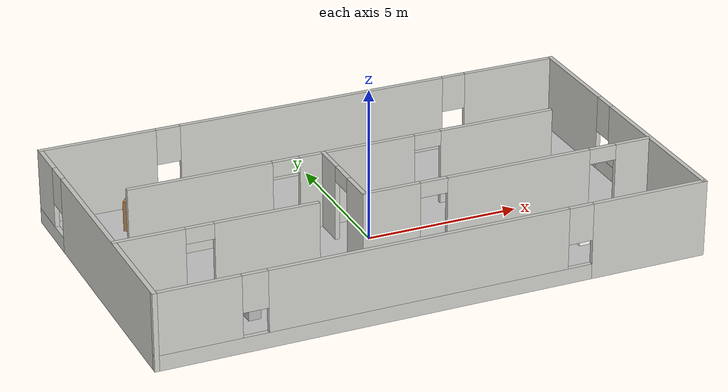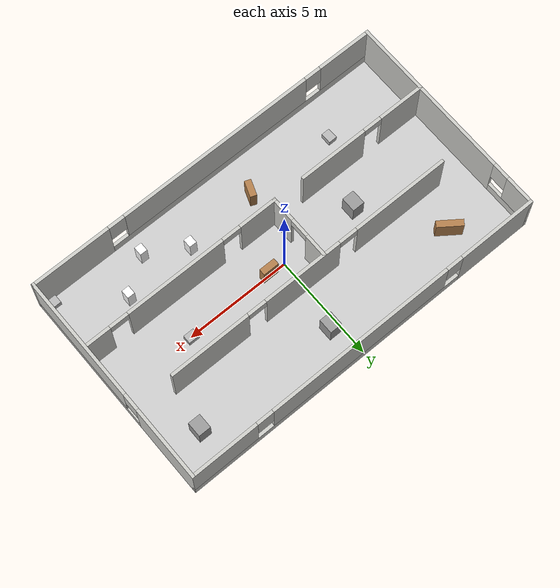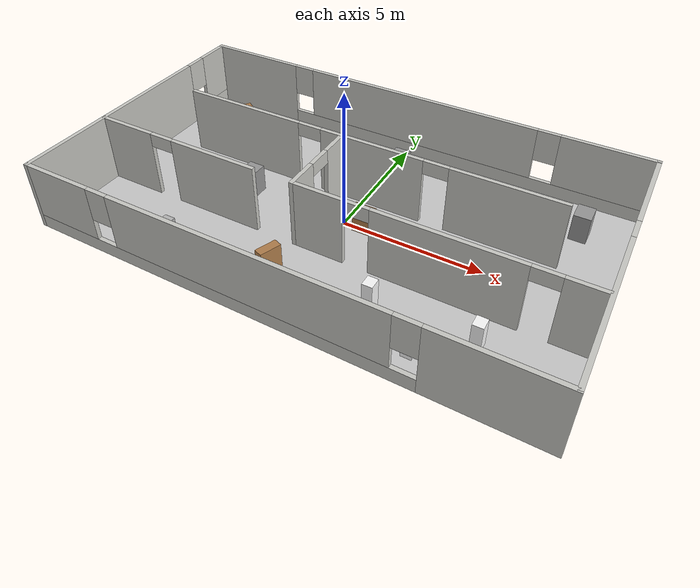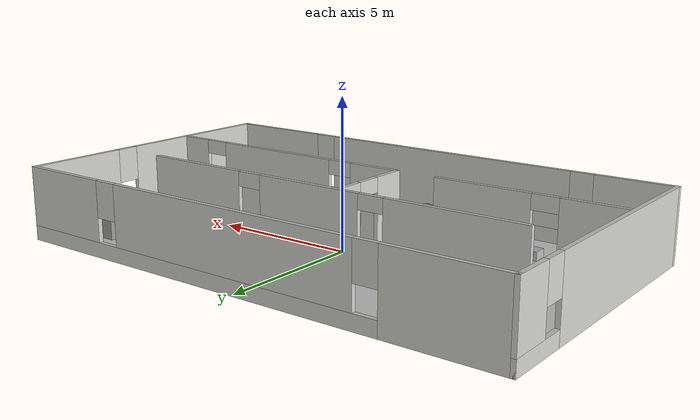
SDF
<?xml version="1.0" ?>
<sdf version="1.5">
  <world name="default">
    <!-- A global light source -->
    <include>
      <uri>model://sun</uri>
    </include>
    <!-- the detected building -->
    <include>
      <uri>model://ground_demap</uri>
    </include>
    <include>
      <uri>model://detectMap</uri>
    </include>
  </world>
</sdf>

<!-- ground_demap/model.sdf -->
<sdf version="1.4">
   <model name="ground_demap">
      <static>true</static>
      <link name="link">
         <collision name="collision">
            <geometry>
               <plane>
                  <normal>0 0 1</normal>
                  <size>17.6 10.15</size>
               </plane>
            </geometry>
            <surface>
               <friction>
                  <ode>
                     <mu>100</mu>
                     <mu2>50</mu2>
                  </ode>
               </friction>
            </surface>
         </collision>

         <visual name="visual">
            <cast_shadows>false</cast_shadows>
            <geometry>
               <plane>
                  <normal>0 0 1</normal>
                  <size>17.6 10.15</size>
               </plane>
            </geometry>
            <material>
               <script>
                  <uri>model://ground_demap/materials/scripts</uri>
                  <uri>model://ground_demap/materials/textures/</uri>
                  <name>MyGroundPlane/Image</name>
               </script>
            </material>
         </visual>
      </link>
   </model>
</sdf>

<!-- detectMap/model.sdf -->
<sdf version='1.7'>
  <model name='detectMap'>
    <link name='Wall_0'>
      <pose>0 5.05 0 0 -0 0</pose>
      <self_collide>0</self_collide>
      <enable_wind>0</enable_wind>
      <kinematic>0</kinematic>
      <visual name='Wall_0_Visual_2'>
        <pose>0.288681 0 1.5 0 -0 0</pose>
        <geometry>
          <box>
            <size>9.07048 0.15 2</size>
          </box>
        </geometry>
        <material>
          <script>
            <uri>file://media/materials/scripts/gazebo.material</uri>
            <name>Gazebo/CeilingTiled</name>
          </script>
          <ambient>1 1 1 1</ambient>
          <shader type='pixel'/>
        </material>
        <meta>
          <layer>0</layer>
        </meta>
        <transparency>0</transparency>
        <cast_shadows>1</cast_shadows>
      </visual>
      <visual name='Wall_0_Visual_5'>
        <pose>5.22392 0 1.9 0 -0 0</pose>
        <geometry>
          <box>
            <size>0.8 0.15 1.2</size>
          </box>
        </geometry>
        <material>
          <script>
            <uri>file://media/materials/scripts/gazebo.material</uri>
            <name>Gazebo/CeilingTiled</name>
          </script>
          <ambient>1 1 1 1</ambient>
          <shader type='pixel'/>
        </material>
        <meta>
          <layer>0</layer>
        </meta>
        <transparency>0</transparency>
        <cast_shadows>1</cast_shadows>
      </visual>
      <visual name='Wall_0_Visual_0'>
        <pose>-6.96078 0 1.25 0 -0 0</pose>
        <geometry>
          <box>
            <size>3.82844 0.15 2.5</size>
          </box>
        </geometry>
        <material>
          <script>
            <uri>file://media/materials/scripts/gazebo.material</uri>
            <name>Gazebo/CeilingTiled</name>
          </script>
          <ambient>1 1 1 1</ambient>
          <shader type='pixel'/>
        </material>
        <meta>
          <layer>0</layer>
        </meta>
        <transparency>0</transparency>
        <cast_shadows>1</cast_shadows>
      </visual>
      <visual name='Wall_0_Visual_1'>
        <pose>1.91422 0 0.25 0 -0 0</pose>
        <geometry>
          <box>
            <size>13.9216 0.15 0.5</size>
          </box>
        </geometry>
        <material>
          <script>
            <uri>file://media/materials/scripts/gazebo.material</uri>
            <name>Gazebo/CeilingTiled</name>
          </script>
          <ambient>1 1 1 1</ambient>
          <shader type='pixel'/>
        </material>
        <meta>
          <layer>0</layer>
        </meta>
        <transparency>0</transparency>
        <cast_shadows>1</cast_shadows>
      </visual>
      <visual name='Wall_0_Visual_4'>
        <pose>-4.64656 0 1.9 0 -0 0</pose>
        <geometry>
          <box>
            <size>0.8 0.15 1.2</size>
          </box>
        </geometry>
        <material>
          <script>
            <uri>file://media/materials/scripts/gazebo.material</uri>
            <name>Gazebo/CeilingTiled</name>
          </script>
          <ambient>1 1 1 1</ambient>
          <shader type='pixel'/>
        </material>
        <meta>
          <layer>0</layer>
        </meta>
        <transparency>0</transparency>
        <cast_shadows>1</cast_shadows>
      </visual>
      <visual name='Wall_0_Visual_3'>
        <pose>7.24946 0 1.5 0 -0 0</pose>
        <geometry>
          <box>
            <size>3.25108 0.15 2</size>
          </box>
        </geometry>
        <material>
          <script>
            <uri>file://media/materials/scripts/gazebo.material</uri>
            <name>Gazebo/CeilingTiled</name>
          </script>
          <ambient>1 1 1 1</ambient>
          <shader type='pixel'/>
        </material>
        <meta>
          <layer>0</layer>
        </meta>
        <transparency>0</transparency>
        <cast_shadows>1</cast_shadows>
      </visual>
      <collision name='Wall_0_Collision_2'>
        <laser_retro>0</laser_retro>
        <max_contacts>10</max_contacts>
        <pose>0.288681 0 1.5 0 -0 0</pose>
        <geometry>
          <box>
            <size>9.07048 0.15 2</size>
          </box>
        </geometry>
        <surface>
          <friction>
            <ode>
              <mu>1</mu>
              <mu2>1</mu2>
              <fdir1>0 0 0</fdir1>
              <slip1>0</slip1>
              <slip2>0</slip2>
            </ode>
            <torsional>
              <coefficient>1</coefficient>
              <patch_radius>0</patch_radius>
              <surface_radius>0</surface_radius>
              <use_patch_radius>1</use_patch_radius>
              <ode>
                <slip>0</slip>
              </ode>
            </torsional>
          </friction>
          <bounce>
            <restitution_coefficient>0</restitution_coefficient>
            <threshold>1e+06</threshold>
          </bounce>
          <contact>
            <collide_without_contact>0</collide_without_contact>
            <collide_without_contact_bitmask>1</collide_without_contact_bitmask>
            <collide_bitmask>1</collide_bitmask>
            <ode>
              <soft_cfm>0</soft_cfm>
              <soft_erp>0.2</soft_erp>
              <kp>1e+13</kp>
              <kd>1</kd>
              <max_vel>0.01</max_vel>
              <min_depth>0</min_depth>
            </ode>
            <bullet>
              <split_impulse>1</split_impulse>
              <split_impulse_penetration_threshold>-0.01</split_impulse_penetration_threshold>
              <soft_cfm>0</soft_cfm>
              <soft_erp>0.2</soft_erp>
              <kp>1e+13</kp>
              <kd>1</kd>
            </bullet>
          </contact>
        </surface>
      </collision>
      <collision name='Wall_0_Collision_5'>
        <laser_retro>0</laser_retro>
        <max_contacts>10</max_contacts>
        <pose>5.22392 0 1.9 0 -0 0</pose>
        <geometry>
          <box>
            <size>0.8 0.15 1.2</size>
          </box>
        </geometry>
        <surface>
          <friction>
            <ode>
              <mu>1</mu>
              <mu2>1</mu2>
              <fdir1>0 0 0</fdir1>
              <slip1>0</slip1>
              <slip2>0</slip2>
            </ode>
            <torsional>
              <coefficient>1</coefficient>
              <patch_radius>0</patch_radius>
              <surface_radius>0</surface_radius>
              <use_patch_radius>1</use_patch_radius>
              <ode>
                <slip>0</slip>
              </ode>
            </torsional>
          </friction>
          <bounce>
            <restitution_coefficient>0</restitution_coefficient>
            <threshold>1e+06</threshold>
          </bounce>
          <contact>
            <collide_without_contact>0</collide_without_contact>
            <collide_without_contact_bitmask>1</collide_without_contact_bitmask>
            <collide_bitmask>1</collide_bitmask>
            <ode>
              <soft_cfm>0</soft_cfm>
              <soft_erp>0.2</soft_erp>
              <kp>1e+13</kp>
              <kd>1</kd>
              <max_vel>0.01</max_vel>
              <min_depth>0</min_depth>
            </ode>
            <bullet>
              <split_impulse>1</split_impulse>
              <split_impulse_penetration_threshold>-0.01</split_impulse_penetration_threshold>
              <soft_cfm>0</soft_cfm>
              <soft_erp>0.2</soft_erp>
              <kp>1e+13</kp>
              <kd>1</kd>
            </bullet>
          </contact>
        </surface>
      </collision>
      <collision name='Wall_0_Collision_1'>
        <laser_retro>0</laser_retro>
        <max_contacts>10</max_contacts>
        <pose>1.91422 0 0.25 0 -0 0</pose>
        <geometry>
          <box>
            <size>13.9216 0.15 0.5</size>
          </box>
        </geometry>
        <surface>
          <friction>
            <ode>
              <mu>1</mu>
              <mu2>1</mu2>
              <fdir1>0 0 0</fdir1>
              <slip1>0</slip1>
              <slip2>0</slip2>
            </ode>
            <torsional>
              <coefficient>1</coefficient>
              <patch_radius>0</patch_radius>
              <surface_radius>0</surface_radius>
              <use_patch_radius>1</use_patch_radius>
              <ode>
                <slip>0</slip>
              </ode>
            </torsional>
          </friction>
          <bounce>
            <restitution_coefficient>0</restitution_coefficient>
            <threshold>1e+06</threshold>
          </bounce>
          <contact>
            <collide_without_contact>0</collide_without_contact>
            <collide_without_contact_bitmask>1</collide_without_contact_bitmask>
            <collide_bitmask>1</collide_bitmask>
            <ode>
              <soft_cfm>0</soft_cfm>
              <soft_erp>0.2</soft_erp>
              <kp>1e+13</kp>
              <kd>1</kd>
              <max_vel>0.01</max_vel>
              <min_depth>0</min_depth>
            </ode>
            <bullet>
              <split_impulse>1</split_impulse>
              <split_impulse_penetration_threshold>-0.01</split_impulse_penetration_threshold>
              <soft_cfm>0</soft_cfm>
              <soft_erp>0.2</soft_erp>
              <kp>1e+13</kp>
              <kd>1</kd>
            </bullet>
          </contact>
        </surface>
      </collision>
      <collision name='Wall_0_Collision_0'>
        <laser_retro>0</laser_retro>
        <max_contacts>10</max_contacts>
        <pose>-6.96078 0 1.25 0 -0 0</pose>
        <geometry>
          <box>
            <size>3.82844 0.15 2.5</size>
          </box>
        </geometry>
        <surface>
          <friction>
            <ode>
              <mu>1</mu>
              <mu2>1</mu2>
              <fdir1>0 0 0</fdir1>
              <slip1>0</slip1>
              <slip2>0</slip2>
            </ode>
            <torsional>
              <coefficient>1</coefficient>
              <patch_radius>0</patch_radius>
              <surface_radius>0</surface_radius>
              <use_patch_radius>1</use_patch_radius>
              <ode>
                <slip>0</slip>
              </ode>
            </torsional>
          </friction>
          <bounce>
            <restitution_coefficient>0</restitution_coefficient>
            <threshold>1e+06</threshold>
          </bounce>
          <contact>
            <collide_without_contact>0</collide_without_contact>
            <collide_without_contact_bitmask>1</collide_without_contact_bitmask>
            <collide_bitmask>1</collide_bitmask>
            <ode>
              <soft_cfm>0</soft_cfm>
              <soft_erp>0.2</soft_erp>
              <kp>1e+13</kp>
              <kd>1</kd>
              <max_vel>0.01</max_vel>
              <min_depth>0</min_depth>
            </ode>
            <bullet>
              <split_impulse>1</split_impulse>
              <split_impulse_penetration_threshold>-0.01</split_impulse_penetration_threshold>
              <soft_cfm>0</soft_cfm>
              <soft_erp>0.2</soft_erp>
              <kp>1e+13</kp>
              <kd>1</kd>
            </bullet>
          </contact>
        </surface>
      </collision>
      <collision name='Wall_0_Collision_4'>
        <laser_retro>0</laser_retro>
        <max_contacts>10</max_contacts>
        <pose>-4.64656 0 1.9 0 -0 0</pose>
        <geometry>
          <box>
            <size>0.8 0.15 1.2</size>
          </box>
        </geometry>
        <surface>
          <friction>
            <ode>
              <mu>1</mu>
              <mu2>1</mu2>
              <fdir1>0 0 0</fdir1>
              <slip1>0</slip1>
              <slip2>0</slip2>
            </ode>
            <torsional>
              <coefficient>1</coefficient>
              <patch_radius>0</patch_radius>
              <surface_radius>0</surface_radius>
              <use_patch_radius>1</use_patch_radius>
              <ode>
                <slip>0</slip>
              </ode>
            </torsional>
          </friction>
          <bounce>
            <restitution_coefficient>0</restitution_coefficient>
            <threshold>1e+06</threshold>
          </bounce>
          <contact>
            <collide_without_contact>0</collide_without_contact>
            <collide_without_contact_bitmask>1</collide_without_contact_bitmask>
            <collide_bitmask>1</collide_bitmask>
            <ode>
              <soft_cfm>0</soft_cfm>
              <soft_erp>0.2</soft_erp>
              <kp>1e+13</kp>
              <kd>1</kd>
              <max_vel>0.01</max_vel>
              <min_depth>0</min_depth>
            </ode>
            <bullet>
              <split_impulse>1</split_impulse>
              <split_impulse_penetration_threshold>-0.01</split_impulse_penetration_threshold>
              <soft_cfm>0</soft_cfm>
              <soft_erp>0.2</soft_erp>
              <kp>1e+13</kp>
              <kd>1</kd>
            </bullet>
          </contact>
        </surface>
      </collision>
      <collision name='Wall_0_Collision_3'>
        <laser_retro>0</laser_retro>
        <max_contacts>10</max_contacts>
        <pose>7.24946 0 1.5 0 -0 0</pose>
        <geometry>
          <box>
            <size>3.25108 0.15 2</size>
          </box>
        </geometry>
        <surface>
          <friction>
            <ode>
              <mu>1</mu>
              <mu2>1</mu2>
              <fdir1>0 0 0</fdir1>
              <slip1>0</slip1>
              <slip2>0</slip2>
            </ode>
            <torsional>
              <coefficient>1</coefficient>
              <patch_radius>0</patch_radius>
              <surface_radius>0</surface_radius>
              <use_patch_radius>1</use_patch_radius>
              <ode>
                <slip>0</slip>
              </ode>
            </torsional>
          </friction>
          <bounce>
            <restitution_coefficient>0</restitution_coefficient>
            <threshold>1e+06</threshold>
          </bounce>
          <contact>
            <collide_without_contact>0</collide_without_contact>
            <collide_without_contact_bitmask>1</collide_without_contact_bitmask>
            <collide_bitmask>1</collide_bitmask>
            <ode>
              <soft_cfm>0</soft_cfm>
              <soft_erp>0.2</soft_erp>
              <kp>1e+13</kp>
              <kd>1</kd>
              <max_vel>0.01</max_vel>
              <min_depth>0</min_depth>
            </ode>
            <bullet>
              <split_impulse>1</split_impulse>
              <split_impulse_penetration_threshold>-0.01</split_impulse_penetration_threshold>
              <soft_cfm>0</soft_cfm>
              <soft_erp>0.2</soft_erp>
              <kp>1e+13</kp>
              <kd>1</kd>
            </bullet>
          </contact>
        </surface>
      </collision>
    </link>
    <link name='Wall_1'>
      <pose>8.8 0 0 0 0 -1.5708</pose>
      <self_collide>0</self_collide>
      <enable_wind>0</enable_wind>
      <kinematic>0</kinematic>
      <visual name='Wall_1_Visual_0'>
        <pose>-3.3782 0 1.25 0 -0 0</pose>
        <geometry>
          <box>
            <size>3.49359 0.15 2.5</size>
          </box>
        </geometry>
        <material>
          <script>
            <uri>file://media/materials/scripts/gazebo.material</uri>
            <name>Gazebo/CeilingTiled</name>
          </script>
          <ambient>1 1 1 1</ambient>
          <shader type='pixel'/>
        </material>
        <meta>
          <layer>0</layer>
        </meta>
        <transparency>0</transparency>
        <cast_shadows>1</cast_shadows>
      </visual>
      <visual name='Wall_1_Visual_2'>
        <pose>2.1468 0 1.5 0 -0 0</pose>
        <geometry>
          <box>
            <size>5.95641 0.15 2</size>
          </box>
        </geometry>
        <material>
          <script>
            <uri>file://media/materials/scripts/gazebo.material</uri>
            <name>Gazebo/CeilingTiled</name>
          </script>
          <ambient>1 1 1 1</ambient>
          <shader type='pixel'/>
        </material>
        <meta>
          <layer>0</layer>
        </meta>
        <transparency>0</transparency>
        <cast_shadows>1</cast_shadows>
      </visual>
      <visual name='Wall_1_Visual_3'>
        <pose>-1.23141 0 1.9 0 -0 0</pose>
        <geometry>
          <box>
            <size>0.8 0.15 1.2</size>
          </box>
        </geometry>
        <material>
          <script>
            <uri>file://media/materials/scripts/gazebo.material</uri>
            <name>Gazebo/CeilingTiled</name>
          </script>
          <ambient>1 1 1 1</ambient>
          <shader type='pixel'/>
        </material>
        <meta>
          <layer>0</layer>
        </meta>
        <transparency>0</transparency>
        <cast_shadows>1</cast_shadows>
      </visual>
      <visual name='Wall_1_Visual_1'>
        <pose>1.7468 0 0.25 0 -0 0</pose>
        <geometry>
          <box>
            <size>6.75641 0.15 0.5</size>
          </box>
        </geometry>
        <material>
          <script>
            <uri>file://media/materials/scripts/gazebo.material</uri>
            <name>Gazebo/CeilingTiled</name>
          </script>
          <ambient>1 1 1 1</ambient>
          <shader type='pixel'/>
        </material>
        <meta>
          <layer>0</layer>
        </meta>
        <transparency>0</transparency>
        <cast_shadows>1</cast_shadows>
      </visual>
      <collision name='Wall_1_Collision_0'>
        <laser_retro>0</laser_retro>
        <max_contacts>10</max_contacts>
        <pose>-3.3782 0 1.25 0 -0 0</pose>
        <geometry>
          <box>
            <size>3.49359 0.15 2.5</size>
          </box>
        </geometry>
        <surface>
          <friction>
            <ode>
              <mu>1</mu>
              <mu2>1</mu2>
              <fdir1>0 0 0</fdir1>
              <slip1>0</slip1>
              <slip2>0</slip2>
            </ode>
            <torsional>
              <coefficient>1</coefficient>
              <patch_radius>0</patch_radius>
              <surface_radius>0</surface_radius>
              <use_patch_radius>1</use_patch_radius>
              <ode>
                <slip>0</slip>
              </ode>
            </torsional>
          </friction>
          <bounce>
            <restitution_coefficient>0</restitution_coefficient>
            <threshold>1e+06</threshold>
          </bounce>
          <contact>
            <collide_without_contact>0</collide_without_contact>
            <collide_without_contact_bitmask>1</collide_without_contact_bitmask>
            <collide_bitmask>1</collide_bitmask>
            <ode>
              <soft_cfm>0</soft_cfm>
              <soft_erp>0.2</soft_erp>
              <kp>1e+13</kp>
              <kd>1</kd>
              <max_vel>0.01</max_vel>
              <min_depth>0</min_depth>
            </ode>
            <bullet>
              <split_impulse>1</split_impulse>
              <split_impulse_penetration_threshold>-0.01</split_impulse_penetration_threshold>
              <soft_cfm>0</soft_cfm>
              <soft_erp>0.2</soft_erp>
              <kp>1e+13</kp>
              <kd>1</kd>
            </bullet>
          </contact>
        </surface>
      </collision>
      <collision name='Wall_1_Collision_2'>
        <laser_retro>0</laser_retro>
        <max_contacts>10</max_contacts>
        <pose>2.1468 0 1.5 0 -0 0</pose>
        <geometry>
          <box>
            <size>5.95641 0.15 2</size>
          </box>
        </geometry>
        <surface>
          <friction>
            <ode>
              <mu>1</mu>
              <mu2>1</mu2>
              <fdir1>0 0 0</fdir1>
              <slip1>0</slip1>
              <slip2>0</slip2>
            </ode>
            <torsional>
              <coefficient>1</coefficient>
              <patch_radius>0</patch_radius>
              <surface_radius>0</surface_radius>
              <use_patch_radius>1</use_patch_radius>
              <ode>
                <slip>0</slip>
              </ode>
            </torsional>
          </friction>
          <bounce>
            <restitution_coefficient>0</restitution_coefficient>
            <threshold>1e+06</threshold>
          </bounce>
          <contact>
            <collide_without_contact>0</collide_without_contact>
            <collide_without_contact_bitmask>1</collide_without_contact_bitmask>
            <collide_bitmask>1</collide_bitmask>
            <ode>
              <soft_cfm>0</soft_cfm>
              <soft_erp>0.2</soft_erp>
              <kp>1e+13</kp>
              <kd>1</kd>
              <max_vel>0.01</max_vel>
              <min_depth>0</min_depth>
            </ode>
            <bullet>
              <split_impulse>1</split_impulse>
              <split_impulse_penetration_threshold>-0.01</split_impulse_penetration_threshold>
              <soft_cfm>0</soft_cfm>
              <soft_erp>0.2</soft_erp>
              <kp>1e+13</kp>
              <kd>1</kd>
            </bullet>
          </contact>
        </surface>
      </collision>
      <collision name='Wall_1_Collision_1'>
        <laser_retro>0</laser_retro>
        <max_contacts>10</max_contacts>
        <pose>1.7468 0 0.25 0 -0 0</pose>
        <geometry>
          <box>
            <size>6.75641 0.15 0.5</size>
          </box>
        </geometry>
        <surface>
          <friction>
            <ode>
              <mu>1</mu>
              <mu2>1</mu2>
              <fdir1>0 0 0</fdir1>
              <slip1>0</slip1>
              <slip2>0</slip2>
            </ode>
            <torsional>
              <coefficient>1</coefficient>
              <patch_radius>0</patch_radius>
              <surface_radius>0</surface_radius>
              <use_patch_radius>1</use_patch_radius>
              <ode>
                <slip>0</slip>
              </ode>
            </torsional>
          </friction>
          <bounce>
            <restitution_coefficient>0</restitution_coefficient>
            <threshold>1e+06</threshold>
          </bounce>
          <contact>
            <collide_without_contact>0</collide_without_contact>
            <collide_without_contact_bitmask>1</collide_without_contact_bitmask>
            <collide_bitmask>1</collide_bitmask>
            <ode>
              <soft_cfm>0</soft_cfm>
              <soft_erp>0.2</soft_erp>
              <kp>1e+13</kp>
              <kd>1</kd>
              <max_vel>0.01</max_vel>
              <min_depth>0</min_depth>
            </ode>
            <bullet>
              <split_impulse>1</split_impulse>
              <split_impulse_penetration_threshold>-0.01</split_impulse_penetration_threshold>
              <soft_cfm>0</soft_cfm>
              <soft_erp>0.2</soft_erp>
              <kp>1e+13</kp>
              <kd>1</kd>
            </bullet>
          </contact>
        </surface>
      </collision>
      <collision name='Wall_1_Collision_3'>
        <laser_retro>0</laser_retro>
        <max_contacts>10</max_contacts>
        <pose>-1.23141 0 1.9 0 -0 0</pose>
        <geometry>
          <box>
            <size>0.8 0.15 1.2</size>
          </box>
        </geometry>
        <surface>
          <friction>
            <ode>
              <mu>1</mu>
              <mu2>1</mu2>
              <fdir1>0 0 0</fdir1>
              <slip1>0</slip1>
              <slip2>0</slip2>
            </ode>
            <torsional>
              <coefficient>1</coefficient>
              <patch_radius>0</patch_radius>
              <surface_radius>0</surface_radius>
              <use_patch_radius>1</use_patch_radius>
              <ode>
                <slip>0</slip>
              </ode>
            </torsional>
          </friction>
          <bounce>
            <restitution_coefficient>0</restitution_coefficient>
            <threshold>1e+06</threshold>
          </bounce>
          <contact>
            <collide_without_contact>0</collide_without_contact>
            <collide_without_contact_bitmask>1</collide_without_contact_bitmask>
            <collide_bitmask>1</collide_bitmask>
            <ode>
              <soft_cfm>0</soft_cfm>
              <soft_erp>0.2</soft_erp>
              <kp>1e+13</kp>
              <kd>1</kd>
              <max_vel>0.01</max_vel>
              <min_depth>0</min_depth>
            </ode>
            <bullet>
              <split_impulse>1</split_impulse>
              <split_impulse_penetration_threshold>-0.01</split_impulse_penetration_threshold>
              <soft_cfm>0</soft_cfm>
              <soft_erp>0.2</soft_erp>
              <kp>1e+13</kp>
              <kd>1</kd>
            </bullet>
          </contact>
        </surface>
      </collision>
    </link>
    <link name='Wall_10'>
      <pose>-5.60751 -1.68367 0 0 -0 0</pose>
      <self_collide>0</self_collide>
      <enable_wind>0</enable_wind>
      <kinematic>0</kinematic>
      <visual name='Wall_10_Visual_2'>
        <pose>-0.545956 0 2.25 0 -0 0</pose>
        <geometry>
          <box>
            <size>0.9 0.15 0.5</size>
          </box>
        </geometry>
        <material>
          <script>
            <uri>file://media/materials/scripts/gazebo.material</uri>
            <name>Gazebo/CeilingTiled</name>
          </script>
          <ambient>1 1 1 1</ambient>
          <shader type='pixel'/>
        </material>
        <meta>
          <layer>0</layer>
        </meta>
        <transparency>0</transparency>
        <cast_shadows>1</cast_shadows>
      </visual>
      <visual name='Wall_10_Visual_0'>
        <pose>-2.12298 0 1.25 0 -0 0</pose>
        <geometry>
          <box>
            <size>2.25404 0.15 2.5</size>
          </box>
        </geometry>
        <material>
          <script>
            <uri>file://media/materials/scripts/gazebo.material</uri>
            <name>Gazebo/CeilingTiled</name>
          </script>
          <ambient>1 1 1 1</ambient>
          <shader type='pixel'/>
        </material>
        <meta>
          <layer>0</layer>
        </meta>
        <transparency>0</transparency>
        <cast_shadows>1</cast_shadows>
      </visual>
      <visual name='Wall_10_Visual_1'>
        <pose>1.57702 0 1.25 0 -0 0</pose>
        <geometry>
          <box>
            <size>3.34596 0.15 2.5</size>
          </box>
        </geometry>
        <material>
          <script>
            <uri>file://media/materials/scripts/gazebo.material</uri>
            <name>Gazebo/CeilingTiled</name>
          </script>
          <ambient>1 1 1 1</ambient>
          <shader type='pixel'/>
        </material>
        <meta>
          <layer>0</layer>
        </meta>
        <transparency>0</transparency>
        <cast_shadows>1</cast_shadows>
      </visual>
      <collision name='Wall_10_Collision_0'>
        <laser_retro>0</laser_retro>
        <max_contacts>10</max_contacts>
        <pose>-2.12298 0 1.25 0 -0 0</pose>
        <geometry>
          <box>
            <size>2.25404 0.15 2.5</size>
          </box>
        </geometry>
        <surface>
          <friction>
            <ode>
              <mu>1</mu>
              <mu2>1</mu2>
              <fdir1>0 0 0</fdir1>
              <slip1>0</slip1>
              <slip2>0</slip2>
            </ode>
            <torsional>
              <coefficient>1</coefficient>
              <patch_radius>0</patch_radius>
              <surface_radius>0</surface_radius>
              <use_patch_radius>1</use_patch_radius>
              <ode>
                <slip>0</slip>
              </ode>
            </torsional>
          </friction>
          <bounce>
            <restitution_coefficient>0</restitution_coefficient>
            <threshold>1e+06</threshold>
          </bounce>
          <contact>
            <collide_without_contact>0</collide_without_contact>
            <collide_without_contact_bitmask>1</collide_without_contact_bitmask>
            <collide_bitmask>1</collide_bitmask>
            <ode>
              <soft_cfm>0</soft_cfm>
              <soft_erp>0.2</soft_erp>
              <kp>1e+13</kp>
              <kd>1</kd>
              <max_vel>0.01</max_vel>
              <min_depth>0</min_depth>
            </ode>
            <bullet>
              <split_impulse>1</split_impulse>
              <split_impulse_penetration_threshold>-0.01</split_impulse_penetration_threshold>
              <soft_cfm>0</soft_cfm>
              <soft_erp>0.2</soft_erp>
              <kp>1e+13</kp>
              <kd>1</kd>
            </bullet>
          </contact>
        </surface>
      </collision>
      <collision name='Wall_10_Collision_2'>
        <laser_retro>0</laser_retro>
        <max_contacts>10</max_contacts>
        <pose>-0.545956 0 2.25 0 -0 0</pose>
        <geometry>
          <box>
            <size>0.9 0.15 0.5</size>
          </box>
        </geometry>
        <surface>
          <friction>
            <ode>
              <mu>1</mu>
              <mu2>1</mu2>
              <fdir1>0 0 0</fdir1>
              <slip1>0</slip1>
              <slip2>0</slip2>
            </ode>
            <torsional>
              <coefficient>1</coefficient>
              <patch_radius>0</patch_radius>
              <surface_radius>0</surface_radius>
              <use_patch_radius>1</use_patch_radius>
              <ode>
                <slip>0</slip>
              </ode>
            </torsional>
          </friction>
          <bounce>
            <restitution_coefficient>0</restitution_coefficient>
            <threshold>1e+06</threshold>
          </bounce>
          <contact>
            <collide_without_contact>0</collide_without_contact>
            <collide_without_contact_bitmask>1</collide_without_contact_bitmask>
            <collide_bitmask>1</collide_bitmask>
            <ode>
              <soft_cfm>0</soft_cfm>
              <soft_erp>0.2</soft_erp>
              <kp>1e+13</kp>
              <kd>1</kd>
              <max_vel>0.01</max_vel>
              <min_depth>0</min_depth>
            </ode>
            <bullet>
              <split_impulse>1</split_impulse>
              <split_impulse_penetration_threshold>-0.01</split_impulse_penetration_threshold>
              <soft_cfm>0</soft_cfm>
              <soft_erp>0.2</soft_erp>
              <kp>1e+13</kp>
              <kd>1</kd>
            </bullet>
          </contact>
        </surface>
      </collision>
      <collision name='Wall_10_Collision_1'>
        <laser_retro>0</laser_retro>
        <max_contacts>10</max_contacts>
        <pose>1.57702 0 1.25 0 -0 0</pose>
        <geometry>
          <box>
            <size>3.34596 0.15 2.5</size>
          </box>
        </geometry>
        <surface>
          <friction>
            <ode>
              <mu>1</mu>
              <mu2>1</mu2>
              <fdir1>0 0 0</fdir1>
              <slip1>0</slip1>
              <slip2>0</slip2>
            </ode>
            <torsional>
              <coefficient>1</coefficient>
              <patch_radius>0</patch_radius>
              <surface_radius>0</surface_radius>
              <use_patch_radius>1</use_patch_radius>
              <ode>
                <slip>0</slip>
              </ode>
            </torsional>
          </friction>
          <bounce>
            <restitution_coefficient>0</restitution_coefficient>
            <threshold>1e+06</threshold>
          </bounce>
          <contact>
            <collide_without_contact>0</collide_without_contact>
            <collide_without_contact_bitmask>1</collide_without_contact_bitmask>
            <collide_bitmask>1</collide_bitmask>
            <ode>
              <soft_cfm>0</soft_cfm>
              <soft_erp>0.2</soft_erp>
              <kp>1e+13</kp>
              <kd>1</kd>
              <max_vel>0.01</max_vel>
              <min_depth>0</min_depth>
            </ode>
            <bullet>
              <split_impulse>1</split_impulse>
              <split_impulse_penetration_threshold>-0.01</split_impulse_penetration_threshold>
              <soft_cfm>0</soft_cfm>
              <soft_erp>0.2</soft_erp>
              <kp>1e+13</kp>
              <kd>1</kd>
            </bullet>
          </contact>
        </surface>
      </collision>
    </link>
    <link name='Wall_12'>
      <pose>-0.894491 -0.143127 0 0 0 -1.5708</pose>
      <self_collide>0</self_collide>
      <enable_wind>0</enable_wind>
      <kinematic>0</kinematic>
      <visual name='Wall_12_Visual_1'>
        <pose>1.0182 0 1.25 0 -0 0</pose>
        <geometry>
          <box>
            <size>1.21361 0.15 2.5</size>
          </box>
        </geometry>
        <material>
          <script>
            <uri>file://media/materials/scripts/gazebo.material</uri>
            <name>Gazebo/CeilingTiled</name>
          </script>
          <ambient>1 1 1 1</ambient>
          <shader type='pixel'/>
        </material>
        <meta>
          <layer>0</layer>
        </meta>
        <transparency>0</transparency>
        <cast_shadows>1</cast_shadows>
      </visual>
      <visual name='Wall_12_Visual_2'>
        <pose>-0.038605 0 2.25 0 -0 0</pose>
        <geometry>
          <box>
            <size>0.9 0.15 0.5</size>
          </box>
        </geometry>
        <material>
          <script>
            <uri>file://media/materials/scripts/gazebo.material</uri>
            <name>Gazebo/CeilingTiled</name>
          </script>
          <ambient>1 1 1 1</ambient>
          <shader type='pixel'/>
        </material>
        <meta>
          <layer>0</layer>
        </meta>
        <transparency>0</transparency>
        <cast_shadows>1</cast_shadows>
      </visual>
      <visual name='Wall_12_Visual_0'>
        <pose>-1.0568 0 1.25 0 -0 0</pose>
        <geometry>
          <box>
            <size>1.1364 0.15 2.5</size>
          </box>
        </geometry>
        <material>
          <script>
            <uri>file://media/materials/scripts/gazebo.material</uri>
            <name>Gazebo/CeilingTiled</name>
          </script>
          <ambient>1 1 1 1</ambient>
          <shader type='pixel'/>
        </material>
        <meta>
          <layer>0</layer>
        </meta>
        <transparency>0</transparency>
        <cast_shadows>1</cast_shadows>
      </visual>
      <collision name='Wall_12_Collision_2'>
        <laser_retro>0</laser_retro>
        <max_contacts>10</max_contacts>
        <pose>-0.038605 0 2.25 0 -0 0</pose>
        <geometry>
          <box>
            <size>0.9 0.15 0.5</size>
          </box>
        </geometry>
        <surface>
          <friction>
            <ode>
              <mu>1</mu>
              <mu2>1</mu2>
              <fdir1>0 0 0</fdir1>
              <slip1>0</slip1>
              <slip2>0</slip2>
            </ode>
            <torsional>
              <coefficient>1</coefficient>
              <patch_radius>0</patch_radius>
              <surface_radius>0</surface_radius>
              <use_patch_radius>1</use_patch_radius>
              <ode>
                <slip>0</slip>
              </ode>
            </torsional>
          </friction>
          <bounce>
            <restitution_coefficient>0</restitution_coefficient>
            <threshold>1e+06</threshold>
          </bounce>
          <contact>
            <collide_without_contact>0</collide_without_contact>
            <collide_without_contact_bitmask>1</collide_without_contact_bitmask>
            <collide_bitmask>1</collide_bitmask>
            <ode>
              <soft_cfm>0</soft_cfm>
              <soft_erp>0.2</soft_erp>
              <kp>1e+13</kp>
              <kd>1</kd>
              <max_vel>0.01</max_vel>
              <min_depth>0</min_depth>
            </ode>
            <bullet>
              <split_impulse>1</split_impulse>
              <split_impulse_penetration_threshold>-0.01</split_impulse_penetration_threshold>
              <soft_cfm>0</soft_cfm>
              <soft_erp>0.2</soft_erp>
              <kp>1e+13</kp>
              <kd>1</kd>
            </bullet>
          </contact>
        </surface>
      </collision>
      <collision name='Wall_12_Collision_0'>
        <laser_retro>0</laser_retro>
        <max_contacts>10</max_contacts>
        <pose>-1.0568 0 1.25 0 -0 0</pose>
        <geometry>
          <box>
            <size>1.1364 0.15 2.5</size>
          </box>
        </geometry>
        <surface>
          <friction>
            <ode>
              <mu>1</mu>
              <mu2>1</mu2>
              <fdir1>0 0 0</fdir1>
              <slip1>0</slip1>
              <slip2>0</slip2>
            </ode>
            <torsional>
              <coefficient>1</coefficient>
              <patch_radius>0</patch_radius>
              <surface_radius>0</surface_radius>
              <use_patch_radius>1</use_patch_radius>
              <ode>
                <slip>0</slip>
              </ode>
            </torsional>
          </friction>
          <bounce>
            <restitution_coefficient>0</restitution_coefficient>
            <threshold>1e+06</threshold>
          </bounce>
          <contact>
            <collide_without_contact>0</collide_without_contact>
            <collide_without_contact_bitmask>1</collide_without_contact_bitmask>
            <collide_bitmask>1</collide_bitmask>
            <ode>
              <soft_cfm>0</soft_cfm>
              <soft_erp>0.2</soft_erp>
              <kp>1e+13</kp>
              <kd>1</kd>
              <max_vel>0.01</max_vel>
              <min_depth>0</min_depth>
            </ode>
            <bullet>
              <split_impulse>1</split_impulse>
              <split_impulse_penetration_threshold>-0.01</split_impulse_penetration_threshold>
              <soft_cfm>0</soft_cfm>
              <soft_erp>0.2</soft_erp>
              <kp>1e+13</kp>
              <kd>1</kd>
            </bullet>
          </contact>
        </surface>
      </collision>
      <collision name='Wall_12_Collision_1'>
        <laser_retro>0</laser_retro>
        <max_contacts>10</max_contacts>
        <pose>1.0182 0 1.25 0 -0 0</pose>
        <geometry>
          <box>
            <size>1.21361 0.15 2.5</size>
          </box>
        </geometry>
        <surface>
          <friction>
            <ode>
              <mu>1</mu>
              <mu2>1</mu2>
              <fdir1>0 0 0</fdir1>
              <slip1>0</slip1>
              <slip2>0</slip2>
            </ode>
            <torsional>
              <coefficient>1</coefficient>
              <patch_radius>0</patch_radius>
              <surface_radius>0</surface_radius>
              <use_patch_radius>1</use_patch_radius>
              <ode>
                <slip>0</slip>
              </ode>
            </torsional>
          </friction>
          <bounce>
            <restitution_coefficient>0</restitution_coefficient>
            <threshold>1e+06</threshold>
          </bounce>
          <contact>
            <collide_without_contact>0</collide_without_contact>
            <collide_without_contact_bitmask>1</collide_without_contact_bitmask>
            <collide_bitmask>1</collide_bitmask>
            <ode>
              <soft_cfm>0</soft_cfm>
              <soft_erp>0.2</soft_erp>
              <kp>1e+13</kp>
              <kd>1</kd>
              <max_vel>0.01</max_vel>
              <min_depth>0</min_depth>
            </ode>
            <bullet>
              <split_impulse>1</split_impulse>
              <split_impulse_penetration_threshold>-0.01</split_impulse_penetration_threshold>
              <soft_cfm>0</soft_cfm>
              <soft_erp>0.2</soft_erp>
              <kp>1e+13</kp>
              <kd>1</kd>
            </bullet>
          </contact>
        </surface>
      </collision>
    </link>
    <link name='Wall_16'>
      <pose>3.90551 -1.69313 0 0 -0 0</pose>
      <self_collide>0</self_collide>
      <enable_wind>0</enable_wind>
      <kinematic>0</kinematic>
      <visual name='Wall_16_Visual_2'>
        <pose>4.26851 0 1.25 0 -0 0</pose>
        <geometry>
          <box>
            <size>1.21298 0.15 2.5</size>
          </box>
        </geometry>
        <material>
          <script>
            <uri>file://media/materials/scripts/gazebo.material</uri>
            <name>Gazebo/CeilingTiled</name>
          </script>
          <ambient>1 1 1 1</ambient>
          <shader type='pixel'/>
        </material>
        <meta>
          <layer>0</layer>
        </meta>
        <transparency>0</transparency>
        <cast_shadows>1</cast_shadows>
      </visual>
      <visual name='Wall_16_Visual_1'>
        <pose>0.342771 0 1.25 0 -0 0</pose>
        <geometry>
          <box>
            <size>4.8385 0.15 2.5</size>
          </box>
        </geometry>
        <material>
          <script>
            <uri>file://media/materials/scripts/gazebo.material</uri>
            <name>Gazebo/CeilingTiled</name>
          </script>
          <ambient>1 1 1 1</ambient>
          <shader type='pixel'/>
        </material>
        <meta>
          <layer>0</layer>
        </meta>
        <transparency>0</transparency>
        <cast_shadows>1</cast_shadows>
      </visual>
      <visual name='Wall_16_Visual_0'>
        <pose>-3.92574 0 1.25 0 -0 0</pose>
        <geometry>
          <box>
            <size>1.89852 0.15 2.5</size>
          </box>
        </geometry>
        <material>
          <script>
            <uri>file://media/materials/scripts/gazebo.material</uri>
            <name>Gazebo/CeilingTiled</name>
          </script>
          <ambient>1 1 1 1</ambient>
          <shader type='pixel'/>
        </material>
        <meta>
          <layer>0</layer>
        </meta>
        <transparency>0</transparency>
        <cast_shadows>1</cast_shadows>
      </visual>
      <visual name='Wall_16_Visual_4'>
        <pose>3.21202 0 2.25 0 -0 0</pose>
        <geometry>
          <box>
            <size>0.9 0.15 0.5</size>
          </box>
        </geometry>
        <material>
          <script>
            <uri>file://media/materials/scripts/gazebo.material</uri>
            <name>Gazebo/CeilingTiled</name>
          </script>
          <ambient>1 1 1 1</ambient>
          <shader type='pixel'/>
        </material>
        <meta>
          <layer>0</layer>
        </meta>
        <transparency>0</transparency>
        <cast_shadows>1</cast_shadows>
      </visual>
      <visual name='Wall_16_Visual_3'>
        <pose>-2.52648 0 2.25 0 -0 0</pose>
        <geometry>
          <box>
            <size>0.9 0.15 0.5</size>
          </box>
        </geometry>
        <material>
          <script>
            <uri>file://media/materials/scripts/gazebo.material</uri>
            <name>Gazebo/CeilingTiled</name>
          </script>
          <ambient>1 1 1 1</ambient>
          <shader type='pixel'/>
        </material>
        <meta>
          <layer>0</layer>
        </meta>
        <transparency>0</transparency>
        <cast_shadows>1</cast_shadows>
      </visual>
      <collision name='Wall_16_Collision_4'>
        <laser_retro>0</laser_retro>
        <max_contacts>10</max_contacts>
        <pose>3.21202 0 2.25 0 -0 0</pose>
        <geometry>
          <box>
            <size>0.9 0.15 0.5</size>
          </box>
        </geometry>
        <surface>
          <friction>
            <ode>
              <mu>1</mu>
              <mu2>1</mu2>
              <fdir1>0 0 0</fdir1>
              <slip1>0</slip1>
              <slip2>0</slip2>
            </ode>
            <torsional>
              <coefficient>1</coefficient>
              <patch_radius>0</patch_radius>
              <surface_radius>0</surface_radius>
              <use_patch_radius>1</use_patch_radius>
              <ode>
                <slip>0</slip>
              </ode>
            </torsional>
          </friction>
          <bounce>
            <restitution_coefficient>0</restitution_coefficient>
            <threshold>1e+06</threshold>
          </bounce>
          <contact>
            <collide_without_contact>0</collide_without_contact>
            <collide_without_contact_bitmask>1</collide_without_contact_bitmask>
            <collide_bitmask>1</collide_bitmask>
            <ode>
              <soft_cfm>0</soft_cfm>
              <soft_erp>0.2</soft_erp>
              <kp>1e+13</kp>
              <kd>1</kd>
              <max_vel>0.01</max_vel>
              <min_depth>0</min_depth>
            </ode>
            <bullet>
              <split_impulse>1</split_impulse>
              <split_impulse_penetration_threshold>-0.01</split_impulse_penetration_threshold>
              <soft_cfm>0</soft_cfm>
              <soft_erp>0.2</soft_erp>
              <kp>1e+13</kp>
              <kd>1</kd>
            </bullet>
          </contact>
        </surface>
      </collision>
      <collision name='Wall_16_Collision_2'>
        <laser_retro>0</laser_retro>
        <max_contacts>10</max_contacts>
        <pose>4.26851 0 1.25 0 -0 0</pose>
        <geometry>
          <box>
            <size>1.21298 0.15 2.5</size>
          </box>
        </geometry>
        <surface>
          <friction>
            <ode>
              <mu>1</mu>
              <mu2>1</mu2>
              <fdir1>0 0 0</fdir1>
              <slip1>0</slip1>
              <slip2>0</slip2>
            </ode>
            <torsional>
              <coefficient>1</coefficient>
              <patch_radius>0</patch_radius>
              <surface_radius>0</surface_radius>
              <use_patch_radius>1</use_patch_radius>
              <ode>
                <slip>0</slip>
              </ode>
            </torsional>
          </friction>
          <bounce>
            <restitution_coefficient>0</restitution_coefficient>
            <threshold>1e+06</threshold>
          </bounce>
          <contact>
            <collide_without_contact>0</collide_without_contact>
            <collide_without_contact_bitmask>1</collide_without_contact_bitmask>
            <collide_bitmask>1</collide_bitmask>
            <ode>
              <soft_cfm>0</soft_cfm>
              <soft_erp>0.2</soft_erp>
              <kp>1e+13</kp>
              <kd>1</kd>
              <max_vel>0.01</max_vel>
              <min_depth>0</min_depth>
            </ode>
            <bullet>
              <split_impulse>1</split_impulse>
              <split_impulse_penetration_threshold>-0.01</split_impulse_penetration_threshold>
              <soft_cfm>0</soft_cfm>
              <soft_erp>0.2</soft_erp>
              <kp>1e+13</kp>
              <kd>1</kd>
            </bullet>
          </contact>
        </surface>
      </collision>
      <collision name='Wall_16_Collision_1'>
        <laser_retro>0</laser_retro>
        <max_contacts>10</max_contacts>
        <pose>0.342771 0 1.25 0 -0 0</pose>
        <geometry>
          <box>
            <size>4.8385 0.15 2.5</size>
          </box>
        </geometry>
        <surface>
          <friction>
            <ode>
              <mu>1</mu>
              <mu2>1</mu2>
              <fdir1>0 0 0</fdir1>
              <slip1>0</slip1>
              <slip2>0</slip2>
            </ode>
            <torsional>
              <coefficient>1</coefficient>
              <patch_radius>0</patch_radius>
              <surface_radius>0</surface_radius>
              <use_patch_radius>1</use_patch_radius>
              <ode>
                <slip>0</slip>
              </ode>
            </torsional>
          </friction>
          <bounce>
            <restitution_coefficient>0</restitution_coefficient>
            <threshold>1e+06</threshold>
          </bounce>
          <contact>
            <collide_without_contact>0</collide_without_contact>
            <collide_without_contact_bitmask>1</collide_without_contact_bitmask>
            <collide_bitmask>1</collide_bitmask>
            <ode>
              <soft_cfm>0</soft_cfm>
              <soft_erp>0.2</soft_erp>
              <kp>1e+13</kp>
              <kd>1</kd>
              <max_vel>0.01</max_vel>
              <min_depth>0</min_depth>
            </ode>
            <bullet>
              <split_impulse>1</split_impulse>
              <split_impulse_penetration_threshold>-0.01</split_impulse_penetration_threshold>
              <soft_cfm>0</soft_cfm>
              <soft_erp>0.2</soft_erp>
              <kp>1e+13</kp>
              <kd>1</kd>
            </bullet>
          </contact>
        </surface>
      </collision>
      <collision name='Wall_16_Collision_3'>
        <laser_retro>0</laser_retro>
        <max_contacts>10</max_contacts>
        <pose>-2.52648 0 2.25 0 -0 0</pose>
        <geometry>
          <box>
            <size>0.9 0.15 0.5</size>
          </box>
        </geometry>
        <surface>
          <friction>
            <ode>
              <mu>1</mu>
              <mu2>1</mu2>
              <fdir1>0 0 0</fdir1>
              <slip1>0</slip1>
              <slip2>0</slip2>
            </ode>
            <torsional>
              <coefficient>1</coefficient>
              <patch_radius>0</patch_radius>
              <surface_radius>0</surface_radius>
              <use_patch_radius>1</use_patch_radius>
              <ode>
                <slip>0</slip>
              </ode>
            </torsional>
          </friction>
          <bounce>
            <restitution_coefficient>0</restitution_coefficient>
            <threshold>1e+06</threshold>
          </bounce>
          <contact>
            <collide_without_contact>0</collide_without_contact>
            <collide_without_contact_bitmask>1</collide_without_contact_bitmask>
            <collide_bitmask>1</collide_bitmask>
            <ode>
              <soft_cfm>0</soft_cfm>
              <soft_erp>0.2</soft_erp>
              <kp>1e+13</kp>
              <kd>1</kd>
              <max_vel>0.01</max_vel>
              <min_depth>0</min_depth>
            </ode>
            <bullet>
              <split_impulse>1</split_impulse>
              <split_impulse_penetration_threshold>-0.01</split_impulse_penetration_threshold>
              <soft_cfm>0</soft_cfm>
              <soft_erp>0.2</soft_erp>
              <kp>1e+13</kp>
              <kd>1</kd>
            </bullet>
          </contact>
        </surface>
      </collision>
      <collision name='Wall_16_Collision_0'>
        <laser_retro>0</laser_retro>
        <max_contacts>10</max_contacts>
        <pose>-3.92574 0 1.25 0 -0 0</pose>
        <geometry>
          <box>
            <size>1.89852 0.15 2.5</size>
          </box>
        </geometry>
        <surface>
          <friction>
            <ode>
              <mu>1</mu>
              <mu2>1</mu2>
              <fdir1>0 0 0</fdir1>
              <slip1>0</slip1>
              <slip2>0</slip2>
            </ode>
            <torsional>
              <coefficient>1</coefficient>
              <patch_radius>0</patch_radius>
              <surface_radius>0</surface_radius>
              <use_patch_radius>1</use_patch_radius>
              <ode>
                <slip>0</slip>
              </ode>
            </torsional>
          </friction>
          <bounce>
            <restitution_coefficient>0</restitution_coefficient>
            <threshold>1e+06</threshold>
          </bounce>
          <contact>
            <collide_without_contact>0</collide_without_contact>
            <collide_without_contact_bitmask>1</collide_without_contact_bitmask>
            <collide_bitmask>1</collide_bitmask>
            <ode>
              <soft_cfm>0</soft_cfm>
              <soft_erp>0.2</soft_erp>
              <kp>1e+13</kp>
              <kd>1</kd>
              <max_vel>0.01</max_vel>
              <min_depth>0</min_depth>
            </ode>
            <bullet>
              <split_impulse>1</split_impulse>
              <split_impulse_penetration_threshold>-0.01</split_impulse_penetration_threshold>
              <soft_cfm>0</soft_cfm>
              <soft_erp>0.2</soft_erp>
              <kp>1e+13</kp>
              <kd>1</kd>
            </bullet>
          </contact>
        </surface>
      </collision>
    </link>
    <link name='Wall_2'>
      <pose>0 -5.05 0 0 -0 3.14159</pose>
      <self_collide>0</self_collide>
      <enable_wind>0</enable_wind>
      <kinematic>0</kinematic>
      <visual name='Wall_2_Visual_3'>
        <pose>7.5235 0 1.5 0 -0 0</pose>
        <geometry>
          <box>
            <size>2.703 0.15 2</size>
          </box>
        </geometry>
        <material>
          <script>
            <uri>file://media/materials/scripts/gazebo.material</uri>
            <name>Gazebo/CeilingTiled</name>
          </script>
          <ambient>1 1 1 1</ambient>
          <shader type='pixel'/>
        </material>
        <meta>
          <layer>0</layer>
        </meta>
        <transparency>0</transparency>
        <cast_shadows>1</cast_shadows>
      </visual>
      <visual name='Wall_2_Visual_0'>
        <pose>-6.95289 0 1.25 0 -0 0</pose>
        <geometry>
          <box>
            <size>3.84422 0.15 2.5</size>
          </box>
        </geometry>
        <material>
          <script>
            <uri>file://media/materials/scripts/gazebo.material</uri>
            <name>Gazebo/CeilingTiled</name>
          </script>
          <ambient>1 1 1 1</ambient>
          <shader type='pixel'/>
        </material>
        <meta>
          <layer>0</layer>
        </meta>
        <transparency>0</transparency>
        <cast_shadows>1</cast_shadows>
      </visual>
      <visual name='Wall_2_Visual_5'>
        <pose>5.77201 0 1.9 0 -0 0</pose>
        <geometry>
          <box>
            <size>0.8 0.15 1.2</size>
          </box>
        </geometry>
        <material>
          <script>
            <uri>file://media/materials/scripts/gazebo.material</uri>
            <name>Gazebo/CeilingTiled</name>
          </script>
          <ambient>1 1 1 1</ambient>
          <shader type='pixel'/>
        </material>
        <meta>
          <layer>0</layer>
        </meta>
        <transparency>0</transparency>
        <cast_shadows>1</cast_shadows>
      </visual>
      <visual name='Wall_2_Visual_1'>
        <pose>1.92211 0 0.25 0 -0 0</pose>
        <geometry>
          <box>
            <size>13.9058 0.15 0.5</size>
          </box>
        </geometry>
        <material>
          <script>
            <uri>file://media/materials/scripts/gazebo.material</uri>
            <name>Gazebo/CeilingTiled</name>
          </script>
          <ambient>1 1 1 1</ambient>
          <shader type='pixel'/>
        </material>
        <meta>
          <layer>0</layer>
        </meta>
        <transparency>0</transparency>
        <cast_shadows>1</cast_shadows>
      </visual>
      <visual name='Wall_2_Visual_2'>
        <pose>0.570613 0 1.5 0 -0 0</pose>
        <geometry>
          <box>
            <size>9.60279 0.15 2</size>
          </box>
        </geometry>
        <material>
          <script>
            <uri>file://media/materials/scripts/gazebo.material</uri>
            <name>Gazebo/CeilingTiled</name>
          </script>
          <ambient>1 1 1 1</ambient>
          <shader type='pixel'/>
        </material>
        <meta>
          <layer>0</layer>
        </meta>
        <transparency>0</transparency>
        <cast_shadows>1</cast_shadows>
      </visual>
      <visual name='Wall_2_Visual_4'>
        <pose>-4.63078 0 1.9 0 -0 0</pose>
        <geometry>
          <box>
            <size>0.8 0.15 1.2</size>
          </box>
        </geometry>
        <material>
          <script>
            <uri>file://media/materials/scripts/gazebo.material</uri>
            <name>Gazebo/CeilingTiled</name>
          </script>
          <ambient>1 1 1 1</ambient>
          <shader type='pixel'/>
        </material>
        <meta>
          <layer>0</layer>
        </meta>
        <transparency>0</transparency>
        <cast_shadows>1</cast_shadows>
      </visual>
      <collision name='Wall_2_Collision_2'>
        <laser_retro>0</laser_retro>
        <max_contacts>10</max_contacts>
        <pose>0.570613 0 1.5 0 -0 0</pose>
        <geometry>
          <box>
            <size>9.60279 0.15 2</size>
          </box>
        </geometry>
        <surface>
          <friction>
            <ode>
              <mu>1</mu>
              <mu2>1</mu2>
              <fdir1>0 0 0</fdir1>
              <slip1>0</slip1>
              <slip2>0</slip2>
            </ode>
            <torsional>
              <coefficient>1</coefficient>
              <patch_radius>0</patch_radius>
              <surface_radius>0</surface_radius>
              <use_patch_radius>1</use_patch_radius>
              <ode>
                <slip>0</slip>
              </ode>
            </torsional>
          </friction>
          <bounce>
            <restitution_coefficient>0</restitution_coefficient>
            <threshold>1e+06</threshold>
          </bounce>
          <contact>
            <collide_without_contact>0</collide_without_contact>
            <collide_without_contact_bitmask>1</collide_without_contact_bitmask>
            <collide_bitmask>1</collide_bitmask>
            <ode>
              <soft_cfm>0</soft_cfm>
              <soft_erp>0.2</soft_erp>
              <kp>1e+13</kp>
              <kd>1</kd>
              <max_vel>0.01</max_vel>
              <min_depth>0</min_depth>
            </ode>
            <bullet>
              <split_impulse>1</split_impulse>
              <split_impulse_penetration_threshold>-0.01</split_impulse_penetration_threshold>
              <soft_cfm>0</soft_cfm>
              <soft_erp>0.2</soft_erp>
              <kp>1e+13</kp>
              <kd>1</kd>
            </bullet>
          </contact>
        </surface>
      </collision>
      <collision name='Wall_2_Collision_0'>
        <laser_retro>0</laser_retro>
        <max_contacts>10</max_contacts>
        <pose>-6.95289 0 1.25 0 -0 0</pose>
        <geometry>
          <box>
            <size>3.84422 0.15 2.5</size>
          </box>
        </geometry>
        <surface>
          <friction>
            <ode>
              <mu>1</mu>
              <mu2>1</mu2>
              <fdir1>0 0 0</fdir1>
              <slip1>0</slip1>
              <slip2>0</slip2>
            </ode>
            <torsional>
              <coefficient>1</coefficient>
              <patch_radius>0</patch_radius>
              <surface_radius>0</surface_radius>
              <use_patch_radius>1</use_patch_radius>
              <ode>
                <slip>0</slip>
              </ode>
            </torsional>
          </friction>
          <bounce>
            <restitution_coefficient>0</restitution_coefficient>
            <threshold>1e+06</threshold>
          </bounce>
          <contact>
            <collide_without_contact>0</collide_without_contact>
            <collide_without_contact_bitmask>1</collide_without_contact_bitmask>
            <collide_bitmask>1</collide_bitmask>
            <ode>
              <soft_cfm>0</soft_cfm>
              <soft_erp>0.2</soft_erp>
              <kp>1e+13</kp>
              <kd>1</kd>
              <max_vel>0.01</max_vel>
              <min_depth>0</min_depth>
            </ode>
            <bullet>
              <split_impulse>1</split_impulse>
              <split_impulse_penetration_threshold>-0.01</split_impulse_penetration_threshold>
              <soft_cfm>0</soft_cfm>
              <soft_erp>0.2</soft_erp>
              <kp>1e+13</kp>
              <kd>1</kd>
            </bullet>
          </contact>
        </surface>
      </collision>
      <collision name='Wall_2_Collision_1'>
        <laser_retro>0</laser_retro>
        <max_contacts>10</max_contacts>
        <pose>1.92211 0 0.25 0 -0 0</pose>
        <geometry>
          <box>
            <size>13.9058 0.15 0.5</size>
          </box>
        </geometry>
        <surface>
          <friction>
            <ode>
              <mu>1</mu>
              <mu2>1</mu2>
              <fdir1>0 0 0</fdir1>
              <slip1>0</slip1>
              <slip2>0</slip2>
            </ode>
            <torsional>
              <coefficient>1</coefficient>
              <patch_radius>0</patch_radius>
              <surface_radius>0</surface_radius>
              <use_patch_radius>1</use_patch_radius>
              <ode>
                <slip>0</slip>
              </ode>
            </torsional>
          </friction>
          <bounce>
            <restitution_coefficient>0</restitution_coefficient>
            <threshold>1e+06</threshold>
          </bounce>
          <contact>
            <collide_without_contact>0</collide_without_contact>
            <collide_without_contact_bitmask>1</collide_without_contact_bitmask>
            <collide_bitmask>1</collide_bitmask>
            <ode>
              <soft_cfm>0</soft_cfm>
              <soft_erp>0.2</soft_erp>
              <kp>1e+13</kp>
              <kd>1</kd>
              <max_vel>0.01</max_vel>
              <min_depth>0</min_depth>
            </ode>
            <bullet>
              <split_impulse>1</split_impulse>
              <split_impulse_penetration_threshold>-0.01</split_impulse_penetration_threshold>
              <soft_cfm>0</soft_cfm>
              <soft_erp>0.2</soft_erp>
              <kp>1e+13</kp>
              <kd>1</kd>
            </bullet>
          </contact>
        </surface>
      </collision>
      <collision name='Wall_2_Collision_3'>
        <laser_retro>0</laser_retro>
        <max_contacts>10</max_contacts>
        <pose>7.5235 0 1.5 0 -0 0</pose>
        <geometry>
          <box>
            <size>2.703 0.15 2</size>
          </box>
        </geometry>
        <surface>
          <friction>
            <ode>
              <mu>1</mu>
              <mu2>1</mu2>
              <fdir1>0 0 0</fdir1>
              <slip1>0</slip1>
              <slip2>0</slip2>
            </ode>
            <torsional>
              <coefficient>1</coefficient>
              <patch_radius>0</patch_radius>
              <surface_radius>0</surface_radius>
              <use_patch_radius>1</use_patch_radius>
              <ode>
                <slip>0</slip>
              </ode>
            </torsional>
          </friction>
          <bounce>
            <restitution_coefficient>0</restitution_coefficient>
            <threshold>1e+06</threshold>
          </bounce>
          <contact>
            <collide_without_contact>0</collide_without_contact>
            <collide_without_contact_bitmask>1</collide_without_contact_bitmask>
            <collide_bitmask>1</collide_bitmask>
            <ode>
              <soft_cfm>0</soft_cfm>
              <soft_erp>0.2</soft_erp>
              <kp>1e+13</kp>
              <kd>1</kd>
              <max_vel>0.01</max_vel>
              <min_depth>0</min_depth>
            </ode>
            <bullet>
              <split_impulse>1</split_impulse>
              <split_impulse_penetration_threshold>-0.01</split_impulse_penetration_threshold>
              <soft_cfm>0</soft_cfm>
              <soft_erp>0.2</soft_erp>
              <kp>1e+13</kp>
              <kd>1</kd>
            </bullet>
          </contact>
        </surface>
      </collision>
      <collision name='Wall_2_Collision_5'>
        <laser_retro>0</laser_retro>
        <max_contacts>10</max_contacts>
        <pose>5.77201 0 1.9 0 -0 0</pose>
        <geometry>
          <box>
            <size>0.8 0.15 1.2</size>
          </box>
        </geometry>
        <surface>
          <friction>
            <ode>
              <mu>1</mu>
              <mu2>1</mu2>
              <fdir1>0 0 0</fdir1>
              <slip1>0</slip1>
              <slip2>0</slip2>
            </ode>
            <torsional>
              <coefficient>1</coefficient>
              <patch_radius>0</patch_radius>
              <surface_radius>0</surface_radius>
              <use_patch_radius>1</use_patch_radius>
              <ode>
                <slip>0</slip>
              </ode>
            </torsional>
          </friction>
          <bounce>
            <restitution_coefficient>0</restitution_coefficient>
            <threshold>1e+06</threshold>
          </bounce>
          <contact>
            <collide_without_contact>0</collide_without_contact>
            <collide_without_contact_bitmask>1</collide_without_contact_bitmask>
            <collide_bitmask>1</collide_bitmask>
            <ode>
              <soft_cfm>0</soft_cfm>
              <soft_erp>0.2</soft_erp>
              <kp>1e+13</kp>
              <kd>1</kd>
              <max_vel>0.01</max_vel>
              <min_depth>0</min_depth>
            </ode>
            <bullet>
              <split_impulse>1</split_impulse>
              <split_impulse_penetration_threshold>-0.01</split_impulse_penetration_threshold>
              <soft_cfm>0</soft_cfm>
              <soft_erp>0.2</soft_erp>
              <kp>1e+13</kp>
              <kd>1</kd>
            </bullet>
          </contact>
        </surface>
      </collision>
      <collision name='Wall_2_Collision_4'>
        <laser_retro>0</laser_retro>
        <max_contacts>10</max_contacts>
        <pose>-4.63078 0 1.9 0 -0 0</pose>
        <geometry>
          <box>
            <size>0.8 0.15 1.2</size>
          </box>
        </geometry>
        <surface>
          <friction>
            <ode>
              <mu>1</mu>
              <mu2>1</mu2>
              <fdir1>0 0 0</fdir1>
              <slip1>0</slip1>
              <slip2>0</slip2>
            </ode>
            <torsional>
              <coefficient>1</coefficient>
              <patch_radius>0</patch_radius>
              <surface_radius>0</surface_radius>
              <use_patch_radius>1</use_patch_radius>
              <ode>
                <slip>0</slip>
              </ode>
            </torsional>
          </friction>
          <bounce>
            <restitution_coefficient>0</restitution_coefficient>
            <threshold>1e+06</threshold>
          </bounce>
          <contact>
            <collide_without_contact>0</collide_without_contact>
            <collide_without_contact_bitmask>1</collide_without_contact_bitmask>
            <collide_bitmask>1</collide_bitmask>
            <ode>
              <soft_cfm>0</soft_cfm>
              <soft_erp>0.2</soft_erp>
              <kp>1e+13</kp>
              <kd>1</kd>
              <max_vel>0.01</max_vel>
              <min_depth>0</min_depth>
            </ode>
            <bullet>
              <split_impulse>1</split_impulse>
              <split_impulse_penetration_threshold>-0.01</split_impulse_penetration_threshold>
              <soft_cfm>0</soft_cfm>
              <soft_erp>0.2</soft_erp>
              <kp>1e+13</kp>
              <kd>1</kd>
            </bullet>
          </contact>
        </surface>
      </collision>
    </link>
    <link name='Wall_3'>
      <pose>-8.8 0 0 0 -0 1.5708</pose>
      <self_collide>0</self_collide>
      <enable_wind>0</enable_wind>
      <kinematic>0</kinematic>
      <visual name='Wall_3_Visual_2'>
        <pose>4.4124 0 1.5 0 -0 0</pose>
        <geometry>
          <box>
            <size>1.4252 0.15 2</size>
          </box>
        </geometry>
        <material>
          <script>
            <uri>file://media/materials/scripts/gazebo.material</uri>
            <name>Gazebo/CeilingTiled</name>
          </script>
          <ambient>1 1 1 1</ambient>
          <shader type='pixel'/>
        </material>
        <meta>
          <layer>0</layer>
        </meta>
        <transparency>0</transparency>
        <cast_shadows>1</cast_shadows>
      </visual>
      <visual name='Wall_3_Visual_0'>
        <pose>-1.1126 0 1.25 0 -0 0</pose>
        <geometry>
          <box>
            <size>8.0248 0.15 2.5</size>
          </box>
        </geometry>
        <material>
          <script>
            <uri>file://media/materials/scripts/gazebo.material</uri>
            <name>Gazebo/CeilingTiled</name>
          </script>
          <ambient>1 1 1 1</ambient>
          <shader type='pixel'/>
        </material>
        <meta>
          <layer>0</layer>
        </meta>
        <transparency>0</transparency>
        <cast_shadows>1</cast_shadows>
      </visual>
      <visual name='Wall_3_Visual_1'>
        <pose>4.0124 0 0.25 0 -0 0</pose>
        <geometry>
          <box>
            <size>2.2252 0.15 0.5</size>
          </box>
        </geometry>
        <material>
          <script>
            <uri>file://media/materials/scripts/gazebo.material</uri>
            <name>Gazebo/CeilingTiled</name>
          </script>
          <ambient>1 1 1 1</ambient>
          <shader type='pixel'/>
        </material>
        <meta>
          <layer>0</layer>
        </meta>
        <transparency>0</transparency>
        <cast_shadows>1</cast_shadows>
      </visual>
      <visual name='Wall_3_Visual_3'>
        <pose>3.2998 0 1.9 0 -0 0</pose>
        <geometry>
          <box>
            <size>0.8 0.15 1.2</size>
          </box>
        </geometry>
        <material>
          <script>
            <uri>file://media/materials/scripts/gazebo.material</uri>
            <name>Gazebo/CeilingTiled</name>
          </script>
          <ambient>1 1 1 1</ambient>
          <shader type='pixel'/>
        </material>
        <meta>
          <layer>0</layer>
        </meta>
        <transparency>0</transparency>
        <cast_shadows>1</cast_shadows>
      </visual>
      <collision name='Wall_3_Collision_1'>
        <laser_retro>0</laser_retro>
        <max_contacts>10</max_contacts>
        <pose>4.0124 0 0.25 0 -0 0</pose>
        <geometry>
          <box>
            <size>2.2252 0.15 0.5</size>
          </box>
        </geometry>
        <surface>
          <friction>
            <ode>
              <mu>1</mu>
              <mu2>1</mu2>
              <fdir1>0 0 0</fdir1>
              <slip1>0</slip1>
              <slip2>0</slip2>
            </ode>
            <torsional>
              <coefficient>1</coefficient>
              <patch_radius>0</patch_radius>
              <surface_radius>0</surface_radius>
              <use_patch_radius>1</use_patch_radius>
              <ode>
                <slip>0</slip>
              </ode>
            </torsional>
          </friction>
          <bounce>
            <restitution_coefficient>0</restitution_coefficient>
            <threshold>1e+06</threshold>
          </bounce>
          <contact>
            <collide_without_contact>0</collide_without_contact>
            <collide_without_contact_bitmask>1</collide_without_contact_bitmask>
            <collide_bitmask>1</collide_bitmask>
            <ode>
              <soft_cfm>0</soft_cfm>
              <soft_erp>0.2</soft_erp>
              <kp>1e+13</kp>
              <kd>1</kd>
              <max_vel>0.01</max_vel>
              <min_depth>0</min_depth>
            </ode>
            <bullet>
              <split_impulse>1</split_impulse>
              <split_impulse_penetration_threshold>-0.01</split_impulse_penetration_threshold>
              <soft_cfm>0</soft_cfm>
              <soft_erp>0.2</soft_erp>
              <kp>1e+13</kp>
              <kd>1</kd>
            </bullet>
          </contact>
        </surface>
      </collision>
      <collision name='Wall_3_Collision_2'>
        <laser_retro>0</laser_retro>
        <max_contacts>10</max_contacts>
        <pose>4.4124 0 1.5 0 -0 0</pose>
        <geometry>
          <box>
            <size>1.4252 0.15 2</size>
          </box>
        </geometry>
        <surface>
          <friction>
            <ode>
              <mu>1</mu>
              <mu2>1</mu2>
              <fdir1>0 0 0</fdir1>
              <slip1>0</slip1>
              <slip2>0</slip2>
            </ode>
            <torsional>
              <coefficient>1</coefficient>
              <patch_radius>0</patch_radius>
              <surface_radius>0</surface_radius>
              <use_patch_radius>1</use_patch_radius>
              <ode>
                <slip>0</slip>
              </ode>
            </torsional>
          </friction>
          <bounce>
            <restitution_coefficient>0</restitution_coefficient>
            <threshold>1e+06</threshold>
          </bounce>
          <contact>
            <collide_without_contact>0</collide_without_contact>
            <collide_without_contact_bitmask>1</collide_without_contact_bitmask>
            <collide_bitmask>1</collide_bitmask>
            <ode>
              <soft_cfm>0</soft_cfm>
              <soft_erp>0.2</soft_erp>
              <kp>1e+13</kp>
              <kd>1</kd>
              <max_vel>0.01</max_vel>
              <min_depth>0</min_depth>
            </ode>
            <bullet>
              <split_impulse>1</split_impulse>
              <split_impulse_penetration_threshold>-0.01</split_impulse_penetration_threshold>
              <soft_cfm>0</soft_cfm>
              <soft_erp>0.2</soft_erp>
              <kp>1e+13</kp>
              <kd>1</kd>
            </bullet>
          </contact>
        </surface>
      </collision>
      <collision name='Wall_3_Collision_3'>
        <laser_retro>0</laser_retro>
        <max_contacts>10</max_contacts>
        <pose>3.2998 0 1.9 0 -0 0</pose>
        <geometry>
          <box>
            <size>0.8 0.15 1.2</size>
          </box>
        </geometry>
        <surface>
          <friction>
            <ode>
              <mu>1</mu>
              <mu2>1</mu2>
              <fdir1>0 0 0</fdir1>
              <slip1>0</slip1>
              <slip2>0</slip2>
            </ode>
            <torsional>
              <coefficient>1</coefficient>
              <patch_radius>0</patch_radius>
              <surface_radius>0</surface_radius>
              <use_patch_radius>1</use_patch_radius>
              <ode>
                <slip>0</slip>
              </ode>
            </torsional>
          </friction>
          <bounce>
            <restitution_coefficient>0</restitution_coefficient>
            <threshold>1e+06</threshold>
          </bounce>
          <contact>
            <collide_without_contact>0</collide_without_contact>
            <collide_without_contact_bitmask>1</collide_without_contact_bitmask>
            <collide_bitmask>1</collide_bitmask>
            <ode>
              <soft_cfm>0</soft_cfm>
              <soft_erp>0.2</soft_erp>
              <kp>1e+13</kp>
              <kd>1</kd>
              <max_vel>0.01</max_vel>
              <min_depth>0</min_depth>
            </ode>
            <bullet>
              <split_impulse>1</split_impulse>
              <split_impulse_penetration_threshold>-0.01</split_impulse_penetration_threshold>
              <soft_cfm>0</soft_cfm>
              <soft_erp>0.2</soft_erp>
              <kp>1e+13</kp>
              <kd>1</kd>
            </bullet>
          </contact>
        </surface>
      </collision>
      <collision name='Wall_3_Collision_0'>
        <laser_retro>0</laser_retro>
        <max_contacts>10</max_contacts>
        <pose>-1.1126 0 1.25 0 -0 0</pose>
        <geometry>
          <box>
            <size>8.0248 0.15 2.5</size>
          </box>
        </geometry>
        <surface>
          <friction>
            <ode>
              <mu>1</mu>
              <mu2>1</mu2>
              <fdir1>0 0 0</fdir1>
              <slip1>0</slip1>
              <slip2>0</slip2>
            </ode>
            <torsional>
              <coefficient>1</coefficient>
              <patch_radius>0</patch_radius>
              <surface_radius>0</surface_radius>
              <use_patch_radius>1</use_patch_radius>
              <ode>
                <slip>0</slip>
              </ode>
            </torsional>
          </friction>
          <bounce>
            <restitution_coefficient>0</restitution_coefficient>
            <threshold>1e+06</threshold>
          </bounce>
          <contact>
            <collide_without_contact>0</collide_without_contact>
            <collide_without_contact_bitmask>1</collide_without_contact_bitmask>
            <collide_bitmask>1</collide_bitmask>
            <ode>
              <soft_cfm>0</soft_cfm>
              <soft_erp>0.2</soft_erp>
              <kp>1e+13</kp>
              <kd>1</kd>
              <max_vel>0.01</max_vel>
              <min_depth>0</min_depth>
            </ode>
            <bullet>
              <split_impulse>1</split_impulse>
              <split_impulse_penetration_threshold>-0.01</split_impulse_penetration_threshold>
              <soft_cfm>0</soft_cfm>
              <soft_erp>0.2</soft_erp>
              <kp>1e+13</kp>
              <kd>1</kd>
            </bullet>
          </contact>
        </surface>
      </collision>
    </link>
    <link name='Wall_6'>
      <pose>-0.177279 1.41197 0 0 -0 0</pose>
      <self_collide>0</self_collide>
      <enable_wind>0</enable_wind>
      <kinematic>0</kinematic>
      <visual name='Wall_6_Visual_3'>
        <pose>-1.97504 0 2.25 0 -0 0</pose>
        <geometry>
          <box>
            <size>0.9 0.15 0.5</size>
          </box>
        </geometry>
        <material>
          <script>
            <uri>file://media/materials/scripts/gazebo.material</uri>
            <name>Gazebo/CeilingTiled</name>
          </script>
          <ambient>1 1 1 1</ambient>
          <shader type='pixel'/>
        </material>
        <meta>
          <layer>0</layer>
        </meta>
        <transparency>0</transparency>
        <cast_shadows>1</cast_shadows>
      </visual>
      <visual name='Wall_6_Visual_2'>
        <pose>5.18015 0 1.25 0 -0 0</pose>
        <geometry>
          <box>
            <size>3.88971 0.15 2.5</size>
          </box>
        </geometry>
        <material>
          <script>
            <uri>file://media/materials/scripts/gazebo.material</uri>
            <name>Gazebo/CeilingTiled</name>
          </script>
          <ambient>1 1 1 1</ambient>
          <shader type='pixel'/>
        </material>
        <meta>
          <layer>0</layer>
        </meta>
        <transparency>0</transparency>
        <cast_shadows>1</cast_shadows>
      </visual>
      <visual name='Wall_6_Visual_0'>
        <pose>-4.77502 0 1.25 0 -0 0</pose>
        <geometry>
          <box>
            <size>4.69996 0.15 2.5</size>
          </box>
        </geometry>
        <material>
          <script>
            <uri>file://media/materials/scripts/gazebo.material</uri>
            <name>Gazebo/CeilingTiled</name>
          </script>
          <ambient>1 1 1 1</ambient>
          <shader type='pixel'/>
        </material>
        <meta>
          <layer>0</layer>
        </meta>
        <transparency>0</transparency>
        <cast_shadows>1</cast_shadows>
      </visual>
      <visual name='Wall_6_Visual_1'>
        <pose>0.405126 0 1.25 0 -0 0</pose>
        <geometry>
          <box>
            <size>3.86034 0.15 2.5</size>
          </box>
        </geometry>
        <material>
          <script>
            <uri>file://media/materials/scripts/gazebo.material</uri>
            <name>Gazebo/CeilingTiled</name>
          </script>
          <ambient>1 1 1 1</ambient>
          <shader type='pixel'/>
        </material>
        <meta>
          <layer>0</layer>
        </meta>
        <transparency>0</transparency>
        <cast_shadows>1</cast_shadows>
      </visual>
      <visual name='Wall_6_Visual_4'>
        <pose>2.7853 0 2.25 0 -0 0</pose>
        <geometry>
          <box>
            <size>0.9 0.15 0.5</size>
          </box>
        </geometry>
        <material>
          <script>
            <uri>file://media/materials/scripts/gazebo.material</uri>
            <name>Gazebo/CeilingTiled</name>
          </script>
          <ambient>1 1 1 1</ambient>
          <shader type='pixel'/>
        </material>
        <meta>
          <layer>0</layer>
        </meta>
        <transparency>0</transparency>
        <cast_shadows>1</cast_shadows>
      </visual>
      <collision name='Wall_6_Collision_4'>
        <laser_retro>0</laser_retro>
        <max_contacts>10</max_contacts>
        <pose>2.7853 0 2.25 0 -0 0</pose>
        <geometry>
          <box>
            <size>0.9 0.15 0.5</size>
          </box>
        </geometry>
        <surface>
          <friction>
            <ode>
              <mu>1</mu>
              <mu2>1</mu2>
              <fdir1>0 0 0</fdir1>
              <slip1>0</slip1>
              <slip2>0</slip2>
            </ode>
            <torsional>
              <coefficient>1</coefficient>
              <patch_radius>0</patch_radius>
              <surface_radius>0</surface_radius>
              <use_patch_radius>1</use_patch_radius>
              <ode>
                <slip>0</slip>
              </ode>
            </torsional>
          </friction>
          <bounce>
            <restitution_coefficient>0</restitution_coefficient>
            <threshold>1e+06</threshold>
          </bounce>
          <contact>
            <collide_without_contact>0</collide_without_contact>
            <collide_without_contact_bitmask>1</collide_without_contact_bitmask>
            <collide_bitmask>1</collide_bitmask>
            <ode>
              <soft_cfm>0</soft_cfm>
              <soft_erp>0.2</soft_erp>
              <kp>1e+13</kp>
              <kd>1</kd>
              <max_vel>0.01</max_vel>
              <min_depth>0</min_depth>
            </ode>
            <bullet>
              <split_impulse>1</split_impulse>
              <split_impulse_penetration_threshold>-0.01</split_impulse_penetration_threshold>
              <soft_cfm>0</soft_cfm>
              <soft_erp>0.2</soft_erp>
              <kp>1e+13</kp>
              <kd>1</kd>
            </bullet>
          </contact>
        </surface>
      </collision>
      <collision name='Wall_6_Collision_0'>
        <laser_retro>0</laser_retro>
        <max_contacts>10</max_contacts>
        <pose>-4.77502 0 1.25 0 -0 0</pose>
        <geometry>
          <box>
            <size>4.69996 0.15 2.5</size>
          </box>
        </geometry>
        <surface>
          <friction>
            <ode>
              <mu>1</mu>
              <mu2>1</mu2>
              <fdir1>0 0 0</fdir1>
              <slip1>0</slip1>
              <slip2>0</slip2>
            </ode>
            <torsional>
              <coefficient>1</coefficient>
              <patch_radius>0</patch_radius>
              <surface_radius>0</surface_radius>
              <use_patch_radius>1</use_patch_radius>
              <ode>
                <slip>0</slip>
              </ode>
            </torsional>
          </friction>
          <bounce>
            <restitution_coefficient>0</restitution_coefficient>
            <threshold>1e+06</threshold>
          </bounce>
          <contact>
            <collide_without_contact>0</collide_without_contact>
            <collide_without_contact_bitmask>1</collide_without_contact_bitmask>
            <collide_bitmask>1</collide_bitmask>
            <ode>
              <soft_cfm>0</soft_cfm>
              <soft_erp>0.2</soft_erp>
              <kp>1e+13</kp>
              <kd>1</kd>
              <max_vel>0.01</max_vel>
              <min_depth>0</min_depth>
            </ode>
            <bullet>
              <split_impulse>1</split_impulse>
              <split_impulse_penetration_threshold>-0.01</split_impulse_penetration_threshold>
              <soft_cfm>0</soft_cfm>
              <soft_erp>0.2</soft_erp>
              <kp>1e+13</kp>
              <kd>1</kd>
            </bullet>
          </contact>
        </surface>
      </collision>
      <collision name='Wall_6_Collision_2'>
        <laser_retro>0</laser_retro>
        <max_contacts>10</max_contacts>
        <pose>5.18015 0 1.25 0 -0 0</pose>
        <geometry>
          <box>
            <size>3.88971 0.15 2.5</size>
          </box>
        </geometry>
        <surface>
          <friction>
            <ode>
              <mu>1</mu>
              <mu2>1</mu2>
              <fdir1>0 0 0</fdir1>
              <slip1>0</slip1>
              <slip2>0</slip2>
            </ode>
            <torsional>
              <coefficient>1</coefficient>
              <patch_radius>0</patch_radius>
              <surface_radius>0</surface_radius>
              <use_patch_radius>1</use_patch_radius>
              <ode>
                <slip>0</slip>
              </ode>
            </torsional>
          </friction>
          <bounce>
            <restitution_coefficient>0</restitution_coefficient>
            <threshold>1e+06</threshold>
          </bounce>
          <contact>
            <collide_without_contact>0</collide_without_contact>
            <collide_without_contact_bitmask>1</collide_without_contact_bitmask>
            <collide_bitmask>1</collide_bitmask>
            <ode>
              <soft_cfm>0</soft_cfm>
              <soft_erp>0.2</soft_erp>
              <kp>1e+13</kp>
              <kd>1</kd>
              <max_vel>0.01</max_vel>
              <min_depth>0</min_depth>
            </ode>
            <bullet>
              <split_impulse>1</split_impulse>
              <split_impulse_penetration_threshold>-0.01</split_impulse_penetration_threshold>
              <soft_cfm>0</soft_cfm>
              <soft_erp>0.2</soft_erp>
              <kp>1e+13</kp>
              <kd>1</kd>
            </bullet>
          </contact>
        </surface>
      </collision>
      <collision name='Wall_6_Collision_1'>
        <laser_retro>0</laser_retro>
        <max_contacts>10</max_contacts>
        <pose>0.405126 0 1.25 0 -0 0</pose>
        <geometry>
          <box>
            <size>3.86034 0.15 2.5</size>
          </box>
        </geometry>
        <surface>
          <friction>
            <ode>
              <mu>1</mu>
              <mu2>1</mu2>
              <fdir1>0 0 0</fdir1>
              <slip1>0</slip1>
              <slip2>0</slip2>
            </ode>
            <torsional>
              <coefficient>1</coefficient>
              <patch_radius>0</patch_radius>
              <surface_radius>0</surface_radius>
              <use_patch_radius>1</use_patch_radius>
              <ode>
                <slip>0</slip>
              </ode>
            </torsional>
          </friction>
          <bounce>
            <restitution_coefficient>0</restitution_coefficient>
            <threshold>1e+06</threshold>
          </bounce>
          <contact>
            <collide_without_contact>0</collide_without_contact>
            <collide_without_contact_bitmask>1</collide_without_contact_bitmask>
            <collide_bitmask>1</collide_bitmask>
            <ode>
              <soft_cfm>0</soft_cfm>
              <soft_erp>0.2</soft_erp>
              <kp>1e+13</kp>
              <kd>1</kd>
              <max_vel>0.01</max_vel>
              <min_depth>0</min_depth>
            </ode>
            <bullet>
              <split_impulse>1</split_impulse>
              <split_impulse_penetration_threshold>-0.01</split_impulse_penetration_threshold>
              <soft_cfm>0</soft_cfm>
              <soft_erp>0.2</soft_erp>
              <kp>1e+13</kp>
              <kd>1</kd>
            </bullet>
          </contact>
        </surface>
      </collision>
      <collision name='Wall_6_Collision_3'>
        <laser_retro>0</laser_retro>
        <max_contacts>10</max_contacts>
        <pose>-1.97504 0 2.25 0 -0 0</pose>
        <geometry>
          <box>
            <size>0.9 0.15 0.5</size>
          </box>
        </geometry>
        <surface>
          <friction>
            <ode>
              <mu>1</mu>
              <mu2>1</mu2>
              <fdir1>0 0 0</fdir1>
              <slip1>0</slip1>
              <slip2>0</slip2>
            </ode>
            <torsional>
              <coefficient>1</coefficient>
              <patch_radius>0</patch_radius>
              <surface_radius>0</surface_radius>
              <use_patch_radius>1</use_patch_radius>
              <ode>
                <slip>0</slip>
              </ode>
            </torsional>
          </friction>
          <bounce>
            <restitution_coefficient>0</restitution_coefficient>
            <threshold>1e+06</threshold>
          </bounce>
          <contact>
            <collide_without_contact>0</collide_without_contact>
            <collide_without_contact_bitmask>1</collide_without_contact_bitmask>
            <collide_bitmask>1</collide_bitmask>
            <ode>
              <soft_cfm>0</soft_cfm>
              <soft_erp>0.2</soft_erp>
              <kp>1e+13</kp>
              <kd>1</kd>
              <max_vel>0.01</max_vel>
              <min_depth>0</min_depth>
            </ode>
            <bullet>
              <split_impulse>1</split_impulse>
              <split_impulse_penetration_threshold>-0.01</split_impulse_penetration_threshold>
              <soft_cfm>0</soft_cfm>
              <soft_erp>0.2</soft_erp>
              <kp>1e+13</kp>
              <kd>1</kd>
            </bullet>
          </contact>
        </surface>
      </collision>
    </link>
    <link name='link_0_1_clone'>
      <inertial>
        <mass>0.14473</mass>
        <inertia>
          <ixx>0.0140681</ixx>
          <ixy>0</ixy>
          <ixz>0</ixz>
          <iyy>0.0135784</iyy>
          <iyz>0</iyz>
          <izz>0.00352488</izz>
        </inertia>
        <pose>0 0 0 0 -0 0</pose>
      </inertial>
      <pose>4.32634 -4.02426 0.5 0 -0 0</pose>
      <self_collide>0</self_collide>
      <enable_wind>0</enable_wind>
      <kinematic>0</kinematic>
      <gravity>1</gravity>
      <visual name='visual_0'>
        <pose>0 0 0 0 -0 0</pose>
        <geometry>
          <box>
            <size>0.354724 0.407957 1</size>
          </box>
        </geometry>
        <material>
          <lighting>1</lighting>
          <script>
            <uri>file://media/materials/scripts/gazebo.material</uri>
            <name>Gazebo/Granite</name>
          </script>
          <shader type='pixel'>
            <normal_map>__default__</normal_map>
          </shader>
          <ambient>0.5 0.5 0.5 1</ambient>
          <diffuse>1 1 1 1</diffuse>
          <specular>0 0 0 1</specular>
          <emissive>0 0 0 1</emissive>
        </material>
        <transparency>0</transparency>
        <cast_shadows>1</cast_shadows>
      </visual>
      <collision name='collision'>
        <laser_retro>0</laser_retro>
        <max_contacts>10</max_contacts>
        <pose>0 0 0 0 -0 0</pose>
        <geometry>
          <box>
            <size>0.354724 0.407957 1</size>
          </box>
        </geometry>
        <surface>
          <friction>
            <ode>
              <mu>1</mu>
              <mu2>1</mu2>
              <fdir1>0 0 0</fdir1>
              <slip1>0</slip1>
              <slip2>0</slip2>
            </ode>
            <torsional>
              <coefficient>1</coefficient>
              <patch_radius>0</patch_radius>
              <surface_radius>0</surface_radius>
              <use_patch_radius>1</use_patch_radius>
              <ode>
                <slip>0</slip>
              </ode>
            </torsional>
          </friction>
          <bounce>
            <restitution_coefficient>0</restitution_coefficient>
            <threshold>1e+06</threshold>
          </bounce>
          <contact>
            <collide_without_contact>0</collide_without_contact>
            <collide_without_contact_bitmask>1</collide_without_contact_bitmask>
            <collide_bitmask>1</collide_bitmask>
            <ode>
              <soft_cfm>0</soft_cfm>
              <soft_erp>0.2</soft_erp>
              <kp>1e+13</kp>
              <kd>1</kd>
              <max_vel>0.01</max_vel>
              <min_depth>0</min_depth>
            </ode>
            <bullet>
              <split_impulse>1</split_impulse>
              <split_impulse_penetration_threshold>-0.01</split_impulse_penetration_threshold>
              <soft_cfm>0</soft_cfm>
              <soft_erp>0.2</soft_erp>
              <kp>1e+13</kp>
              <kd>1</kd>
            </bullet>
          </contact>
        </surface>
      </collision>
    </link>
    <link name='link_0_1_clone_0'>
      <inertial>
        <mass>0.14473</mass>
        <inertia>
          <ixx>0.0140681</ixx>
          <ixy>0</ixy>
          <ixz>0</ixz>
          <iyy>0.0135784</iyy>
          <iyz>0</iyz>
          <izz>0.00352488</izz>
        </inertia>
        <pose>0 0 0 0 -0 0</pose>
      </inertial>
      <pose>5.87795 -2.88069 0.5 0 -0 0</pose>
      <self_collide>0</self_collide>
      <enable_wind>0</enable_wind>
      <kinematic>0</kinematic>
      <gravity>1</gravity>
      <visual name='visual_0'>
        <pose>0 0 0 0 -0 0</pose>
        <geometry>
          <box>
            <size>0.354724 0.407957 1</size>
          </box>
        </geometry>
        <material>
          <lighting>1</lighting>
          <script>
            <uri>file://media/materials/scripts/gazebo.material</uri>
            <name>Gazebo/Granite</name>
          </script>
          <shader type='pixel'>
            <normal_map>__default__</normal_map>
          </shader>
          <ambient>0.5 0.5 0.5 1</ambient>
          <diffuse>1 1 1 1</diffuse>
          <specular>0 0 0 1</specular>
          <emissive>0 0 0 1</emissive>
        </material>
        <transparency>0</transparency>
        <cast_shadows>1</cast_shadows>
      </visual>
      <collision name='collision'>
        <laser_retro>0</laser_retro>
        <max_contacts>10</max_contacts>
        <pose>0 0 0 0 -0 0</pose>
        <geometry>
          <box>
            <size>0.354724 0.407957 1</size>
          </box>
        </geometry>
        <surface>
          <friction>
            <ode>
              <mu>1</mu>
              <mu2>1</mu2>
              <fdir1>0 0 0</fdir1>
              <slip1>0</slip1>
              <slip2>0</slip2>
            </ode>
            <torsional>
              <coefficient>1</coefficient>
              <patch_radius>0</patch_radius>
              <surface_radius>0</surface_radius>
              <use_patch_radius>1</use_patch_radius>
              <ode>
                <slip>0</slip>
              </ode>
            </torsional>
          </friction>
          <bounce>
            <restitution_coefficient>0</restitution_coefficient>
            <threshold>1e+06</threshold>
          </bounce>
          <contact>
            <collide_without_contact>0</collide_without_contact>
            <collide_without_contact_bitmask>1</collide_without_contact_bitmask>
            <collide_bitmask>1</collide_bitmask>
            <ode>
              <soft_cfm>0</soft_cfm>
              <soft_erp>0.2</soft_erp>
              <kp>1e+13</kp>
              <kd>1</kd>
              <max_vel>0.01</max_vel>
              <min_depth>0</min_depth>
            </ode>
            <bullet>
              <split_impulse>1</split_impulse>
              <split_impulse_penetration_threshold>-0.01</split_impulse_penetration_threshold>
              <soft_cfm>0</soft_cfm>
              <soft_erp>0.2</soft_erp>
              <kp>1e+13</kp>
              <kd>1</kd>
            </bullet>
          </contact>
        </surface>
      </collision>
    </link>
    <link name='link_0_1_clone_clone'>
      <inertial>
        <mass>0.14473</mass>
        <inertia>
          <ixx>0.0140681</ixx>
          <ixy>0</ixy>
          <ixz>0</ixz>
          <iyy>0.0135784</iyy>
          <iyz>0</iyz>
          <izz>0.00352488</izz>
        </inertia>
        <pose>0 0 0 0 -0 0</pose>
      </inertial>
      <pose>2.55874 -2.99096 0.5 0 -0 0</pose>
      <self_collide>0</self_collide>
      <enable_wind>0</enable_wind>
      <kinematic>0</kinematic>
      <gravity>1</gravity>
      <visual name='visual_0'>
        <pose>0 0 0 0 -0 0</pose>
        <geometry>
          <box>
            <size>0.354724 0.407957 1</size>
          </box>
        </geometry>
        <material>
          <lighting>1</lighting>
          <script>
            <uri>file://media/materials/scripts/gazebo.material</uri>
            <name>Gazebo/Granite</name>
          </script>
          <shader type='pixel'>
            <normal_map>__default__</normal_map>
          </shader>
          <ambient>0.5 0.5 0.5 1</ambient>
          <diffuse>1 1 1 1</diffuse>
          <specular>0 0 0 1</specular>
          <emissive>0 0 0 1</emissive>
        </material>
        <transparency>0</transparency>
        <cast_shadows>1</cast_shadows>
      </visual>
      <collision name='collision'>
        <laser_retro>0</laser_retro>
        <max_contacts>10</max_contacts>
        <pose>0 0 0 0 -0 0</pose>
        <geometry>
          <box>
            <size>0.354724 0.407957 1</size>
          </box>
        </geometry>
        <surface>
          <friction>
            <ode>
              <mu>1</mu>
              <mu2>1</mu2>
              <fdir1>0 0 0</fdir1>
              <slip1>0</slip1>
              <slip2>0</slip2>
            </ode>
            <torsional>
              <coefficient>1</coefficient>
              <patch_radius>0</patch_radius>
              <surface_radius>0</surface_radius>
              <use_patch_radius>1</use_patch_radius>
              <ode>
                <slip>0</slip>
              </ode>
            </torsional>
          </friction>
          <bounce>
            <restitution_coefficient>0</restitution_coefficient>
            <threshold>1e+06</threshold>
          </bounce>
          <contact>
            <collide_without_contact>0</collide_without_contact>
            <collide_without_contact_bitmask>1</collide_without_contact_bitmask>
            <collide_bitmask>1</collide_bitmask>
            <ode>
              <soft_cfm>0</soft_cfm>
              <soft_erp>0.2</soft_erp>
              <kp>1e+13</kp>
              <kd>1</kd>
              <max_vel>0.01</max_vel>
              <min_depth>0</min_depth>
            </ode>
            <bullet>
              <split_impulse>1</split_impulse>
              <split_impulse_penetration_threshold>-0.01</split_impulse_penetration_threshold>
              <soft_cfm>0</soft_cfm>
              <soft_erp>0.2</soft_erp>
              <kp>1e+13</kp>
              <kd>1</kd>
            </bullet>
          </contact>
        </surface>
      </collision>
    </link>
    <link name='link_2'>
      <inertial>
        <mass>0.232568</mass>
        <inertia>
          <ixx>0.0307465</ixx>
          <ixy>0</ixy>
          <ixz>0</ixz>
          <iyy>0.0211682</iyy>
          <iyz>0</iyz>
          <izz>0.0131533</izz>
        </inertia>
        <pose>0 0 0 0 -0 0</pose>
      </inertial>
      <pose>-0.857606 -3.21584 0.5 0 0 -0.355795</pose>
      <gravity>1</gravity>
      <self_collide>0</self_collide>
      <kinematic>0</kinematic>
      <enable_wind>0</enable_wind>
      <visual name='visual'>
        <pose>0 0 0 0 -0 0</pose>
        <geometry>
          <box>
            <size>0.303696 0.765801 1</size>
          </box>
        </geometry>
        <material>
          <lighting>1</lighting>
          <script>
            <uri>file://media/materials/scripts/gazebo.material</uri>
            <name>Gazebo/Wood</name>
          </script>
          <shader type='pixel'>
            <normal_map>__default__</normal_map>
          </shader>
          <ambient>1 1 1 1</ambient>
          <diffuse>1 1 1 1</diffuse>
          <specular>0.2 0.2 0.2 1</specular>
          <emissive>0 0 0 1</emissive>
        </material>
        <transparency>0</transparency>
        <cast_shadows>1</cast_shadows>
      </visual>
      <collision name='collision'>
        <laser_retro>0</laser_retro>
        <max_contacts>10</max_contacts>
        <pose>0 0 0 0 -0 0</pose>
        <geometry>
          <box>
            <size>0.303696 0.765801 1</size>
          </box>
        </geometry>
        <surface>
          <friction>
            <ode>
              <mu>1</mu>
              <mu2>1</mu2>
              <fdir1>0 0 0</fdir1>
              <slip1>0</slip1>
              <slip2>0</slip2>
            </ode>
            <torsional>
              <coefficient>1</coefficient>
              <patch_radius>0</patch_radius>
              <surface_radius>0</surface_radius>
              <use_patch_radius>1</use_patch_radius>
              <ode>
                <slip>0</slip>
              </ode>
            </torsional>
          </friction>
          <bounce>
            <restitution_coefficient>0</restitution_coefficient>
            <threshold>1e+06</threshold>
          </bounce>
          <contact>
            <collide_without_contact>0</collide_without_contact>
            <collide_without_contact_bitmask>1</collide_without_contact_bitmask>
            <collide_bitmask>1</collide_bitmask>
            <ode>
              <soft_cfm>0</soft_cfm>
              <soft_erp>0.2</soft_erp>
              <kp>1e+13</kp>
              <kd>1</kd>
              <max_vel>0.01</max_vel>
              <min_depth>0</min_depth>
            </ode>
            <bullet>
              <split_impulse>1</split_impulse>
              <split_impulse_penetration_threshold>-0.01</split_impulse_penetration_threshold>
              <soft_cfm>0</soft_cfm>
              <soft_erp>0.2</soft_erp>
              <kp>1e+13</kp>
              <kd>1</kd>
            </bullet>
          </contact>
        </surface>
      </collision>
    </link>
    <link name='link_2_clone'>
      <inertial>
        <mass>0.358474</mass>
        <inertia>
          <ixx>0.0714948</ixx>
          <ixy>0</ixy>
          <ixz>0</ixz>
          <iyy>0.032628</iyy>
          <iyz>0</iyz>
          <izz>0.0443771</izz>
        </inertia>
        <pose>0 0 0 0 -0 0</pose>
      </inertial>
      <pose>-6.16625 3.29887 0.5 0 -0 0.940401</pose>
      <gravity>1</gravity>
      <self_collide>0</self_collide>
      <kinematic>0</kinematic>
      <enable_wind>0</enable_wind>
      <visual name='visual'>
        <pose>0 0 0 0 -0 0</pose>
        <geometry>
          <box>
            <size>0.303696 1.18038 1</size>
          </box>
        </geometry>
        <material>
          <lighting>1</lighting>
          <script>
            <uri>file://media/materials/scripts/gazebo.material</uri>
            <name>Gazebo/Wood</name>
          </script>
          <shader type='pixel'>
            <normal_map>__default__</normal_map>
          </shader>
          <ambient>1 1 1 1</ambient>
          <diffuse>1 1 1 1</diffuse>
          <specular>0.2 0.2 0.2 1</specular>
          <emissive>0 0 0 1</emissive>
        </material>
        <transparency>0</transparency>
        <cast_shadows>1</cast_shadows>
      </visual>
      <collision name='collision'>
        <laser_retro>0</laser_retro>
        <max_contacts>10</max_contacts>
        <pose>0 0 0 0 -0 0</pose>
        <geometry>
          <box>
            <size>0.303696 1.18038 1</size>
          </box>
        </geometry>
        <surface>
          <friction>
            <ode>
              <mu>1</mu>
              <mu2>1</mu2>
              <fdir1>0 0 0</fdir1>
              <slip1>0</slip1>
              <slip2>0</slip2>
            </ode>
            <torsional>
              <coefficient>1</coefficient>
              <patch_radius>0</patch_radius>
              <surface_radius>0</surface_radius>
              <use_patch_radius>1</use_patch_radius>
              <ode>
                <slip>0</slip>
              </ode>
            </torsional>
          </friction>
          <bounce>
            <restitution_coefficient>0</restitution_coefficient>
            <threshold>1e+06</threshold>
          </bounce>
          <contact>
            <collide_without_contact>0</collide_without_contact>
            <collide_without_contact_bitmask>1</collide_without_contact_bitmask>
            <collide_bitmask>1</collide_bitmask>
            <ode>
              <soft_cfm>0</soft_cfm>
              <soft_erp>0.2</soft_erp>
              <kp>1e+13</kp>
              <kd>1</kd>
              <max_vel>0.01</max_vel>
              <min_depth>0</min_depth>
            </ode>
            <bullet>
              <split_impulse>1</split_impulse>
              <split_impulse_penetration_threshold>-0.01</split_impulse_penetration_threshold>
              <soft_cfm>0</soft_cfm>
              <soft_erp>0.2</soft_erp>
              <kp>1e+13</kp>
              <kd>1</kd>
            </bullet>
          </contact>
        </surface>
      </collision>
    </link>
    <link name='link_2_clone_0'>
      <inertial>
        <mass>0.232568</mass>
        <inertia>
          <ixx>0.0307465</ixx>
          <ixy>0</ixy>
          <ixz>0</ixz>
          <iyy>0.0211682</iyy>
          <iyz>0</iyz>
          <izz>0.0131533</izz>
        </inertia>
        <pose>0 0 0 0 -0 0</pose>
      </inertial>
      <pose>0.789125 -0.038063 0.5 0 0 -1.56989</pose>
      <gravity>1</gravity>
      <self_collide>0</self_collide>
      <kinematic>0</kinematic>
      <enable_wind>0</enable_wind>
      <visual name='visual'>
        <pose>0 0 0 0 -0 0</pose>
        <geometry>
          <box>
            <size>0.303696 0.765801 1</size>
          </box>
        </geometry>
        <material>
          <lighting>1</lighting>
          <script>
            <uri>file://media/materials/scripts/gazebo.material</uri>
            <name>Gazebo/Wood</name>
          </script>
          <shader type='pixel'>
            <normal_map>__default__</normal_map>
          </shader>
          <ambient>1 1 1 1</ambient>
          <diffuse>1 1 1 1</diffuse>
          <specular>0.2 0.2 0.2 1</specular>
          <emissive>0 0 0 1</emissive>
        </material>
        <transparency>0</transparency>
        <cast_shadows>1</cast_shadows>
      </visual>
      <collision name='collision'>
        <laser_retro>0</laser_retro>
        <max_contacts>10</max_contacts>
        <pose>0 0 0 0 -0 0</pose>
        <geometry>
          <box>
            <size>0.303696 0.765801 1</size>
          </box>
        </geometry>
        <surface>
          <friction>
            <ode>
              <mu>1</mu>
              <mu2>1</mu2>
              <fdir1>0 0 0</fdir1>
              <slip1>0</slip1>
              <slip2>0</slip2>
            </ode>
            <torsional>
              <coefficient>1</coefficient>
              <patch_radius>0</patch_radius>
              <surface_radius>0</surface_radius>
              <use_patch_radius>1</use_patch_radius>
              <ode>
                <slip>0</slip>
              </ode>
            </torsional>
          </friction>
          <bounce>
            <restitution_coefficient>0</restitution_coefficient>
            <threshold>1e+06</threshold>
          </bounce>
          <contact>
            <collide_without_contact>0</collide_without_contact>
            <collide_without_contact_bitmask>1</collide_without_contact_bitmask>
            <collide_bitmask>1</collide_bitmask>
            <ode>
              <soft_cfm>0</soft_cfm>
              <soft_erp>0.2</soft_erp>
              <kp>1e+13</kp>
              <kd>1</kd>
              <max_vel>0.01</max_vel>
              <min_depth>0</min_depth>
            </ode>
            <bullet>
              <split_impulse>1</split_impulse>
              <split_impulse_penetration_threshold>-0.01</split_impulse_penetration_threshold>
              <soft_cfm>0</soft_cfm>
              <soft_erp>0.2</soft_erp>
              <kp>1e+13</kp>
              <kd>1</kd>
            </bullet>
          </contact>
        </surface>
      </collision>
    </link>
    <link name='link_3'>
      <inertial>
        <mass>0.403217</mass>
        <inertia>
          <ixx>0.0497169</ixx>
          <ixy>0</ixy>
          <ixz>0</ixz>
          <iyy>0.0449921</iyy>
          <iyz>0</iyz>
          <izz>0.0275061</izz>
        </inertia>
        <pose>0 0 0 0 -0 0</pose>
      </inertial>
      <pose>-3.76267 -0.029797 0.5 0 -0 0</pose>
      <gravity>1</gravity>
      <self_collide>0</self_collide>
      <kinematic>0</kinematic>
      <enable_wind>0</enable_wind>
      <visual name='visual'>
        <pose>0 0 0 0 -0 0</pose>
        <geometry>
          <box>
            <size>0.582232 0.692536 1</size>
          </box>
        </geometry>
        <material>
          <lighting>1</lighting>
          <script>
            <uri>file://media/materials/scripts/gazebo.material</uri>
            <name>Gazebo/Grey</name>
          </script>
          <shader type='pixel'>
            <normal_map>__default__</normal_map>
          </shader>
          <ambient>1 1 1 1</ambient>
          <diffuse>1 1 1 1</diffuse>
          <specular>0.2 0.2 0.2 1</specular>
          <emissive>0 0 0 1</emissive>
        </material>
        <transparency>0</transparency>
        <cast_shadows>1</cast_shadows>
      </visual>
      <collision name='collision'>
        <laser_retro>0</laser_retro>
        <max_contacts>10</max_contacts>
        <pose>0 0 0 0 -0 0</pose>
        <geometry>
          <box>
            <size>0.582232 0.692536 1</size>
          </box>
        </geometry>
        <surface>
          <friction>
            <ode>
              <mu>1</mu>
              <mu2>1</mu2>
              <fdir1>0 0 0</fdir1>
              <slip1>0</slip1>
              <slip2>0</slip2>
            </ode>
            <torsional>
              <coefficient>1</coefficient>
              <patch_radius>0</patch_radius>
              <surface_radius>0</surface_radius>
              <use_patch_radius>1</use_patch_radius>
              <ode>
                <slip>0</slip>
              </ode>
            </torsional>
          </friction>
          <bounce>
            <restitution_coefficient>0</restitution_coefficient>
            <threshold>1e+06</threshold>
          </bounce>
          <contact>
            <collide_without_contact>0</collide_without_contact>
            <collide_without_contact_bitmask>1</collide_without_contact_bitmask>
            <collide_bitmask>1</collide_bitmask>
            <ode>
              <soft_cfm>0</soft_cfm>
              <soft_erp>0.2</soft_erp>
              <kp>1e+13</kp>
              <kd>1</kd>
              <max_vel>0.01</max_vel>
              <min_depth>0</min_depth>
            </ode>
            <bullet>
              <split_impulse>1</split_impulse>
              <split_impulse_penetration_threshold>-0.01</split_impulse_penetration_threshold>
              <soft_cfm>0</soft_cfm>
              <soft_erp>0.2</soft_erp>
              <kp>1e+13</kp>
              <kd>1</kd>
            </bullet>
          </contact>
        </surface>
      </collision>
    </link>
    <link name='link_3_clone'>
      <inertial>
        <mass>0.403217</mass>
        <inertia>
          <ixx>0.0497169</ixx>
          <ixy>0</ixy>
          <ixz>0</ixz>
          <iyy>0.0449921</iyy>
          <iyz>0</iyz>
          <izz>0.0275061</izz>
        </inertia>
        <pose>0 0 0 0 -0 0</pose>
      </inertial>
      <pose>0.405845 3.39945 0.5 0 -0 0</pose>
      <gravity>1</gravity>
      <self_collide>0</self_collide>
      <kinematic>0</kinematic>
      <enable_wind>0</enable_wind>
      <visual name='visual'>
        <pose>0 0 0 0 -0 0</pose>
        <geometry>
          <box>
            <size>0.582232 0.692536 1</size>
          </box>
        </geometry>
        <material>
          <lighting>1</lighting>
          <script>
            <uri>file://media/materials/scripts/gazebo.material</uri>
            <name>Gazebo/Grey</name>
          </script>
          <shader type='pixel'>
            <normal_map>__default__</normal_map>
          </shader>
          <ambient>1 1 1 1</ambient>
          <diffuse>1 1 1 1</diffuse>
          <specular>0.2 0.2 0.2 1</specular>
          <emissive>0 0 0 1</emissive>
        </material>
        <transparency>0</transparency>
        <cast_shadows>1</cast_shadows>
      </visual>
      <collision name='collision'>
        <laser_retro>0</laser_retro>
        <max_contacts>10</max_contacts>
        <pose>0 0 0 0 -0 0</pose>
        <geometry>
          <box>
            <size>0.582232 0.692536 1</size>
          </box>
        </geometry>
        <surface>
          <friction>
            <ode>
              <mu>1</mu>
              <mu2>1</mu2>
              <fdir1>0 0 0</fdir1>
              <slip1>0</slip1>
              <slip2>0</slip2>
            </ode>
            <torsional>
              <coefficient>1</coefficient>
              <patch_radius>0</patch_radius>
              <surface_radius>0</surface_radius>
              <use_patch_radius>1</use_patch_radius>
              <ode>
                <slip>0</slip>
              </ode>
            </torsional>
          </friction>
          <bounce>
            <restitution_coefficient>0</restitution_coefficient>
            <threshold>1e+06</threshold>
          </bounce>
          <contact>
            <collide_without_contact>0</collide_without_contact>
            <collide_without_contact_bitmask>1</collide_without_contact_bitmask>
            <collide_bitmask>1</collide_bitmask>
            <ode>
              <soft_cfm>0</soft_cfm>
              <soft_erp>0.2</soft_erp>
              <kp>1e+13</kp>
              <kd>1</kd>
              <max_vel>0.01</max_vel>
              <min_depth>0</min_depth>
            </ode>
            <bullet>
              <split_impulse>1</split_impulse>
              <split_impulse_penetration_threshold>-0.01</split_impulse_penetration_threshold>
              <soft_cfm>0</soft_cfm>
              <soft_erp>0.2</soft_erp>
              <kp>1e+13</kp>
              <kd>1</kd>
            </bullet>
          </contact>
        </surface>
      </collision>
    </link>
    <link name='link_3_clone_clone'>
      <inertial>
        <mass>0.403217</mass>
        <inertia>
          <ixx>0.0497169</ixx>
          <ixy>0</ixy>
          <ixz>0</ixz>
          <iyy>0.0449921</iyy>
          <iyz>0</iyz>
          <izz>0.0275061</izz>
        </inertia>
        <pose>0 0 0 0 -0 0</pose>
      </inertial>
      <pose>7.16113 3.31085 0.5 0 -0 0</pose>
      <gravity>1</gravity>
      <self_collide>0</self_collide>
      <kinematic>0</kinematic>
      <enable_wind>0</enable_wind>
      <visual name='visual'>
        <pose>0 0 0 0 -0 0</pose>
        <geometry>
          <box>
            <size>0.582232 0.692536 1</size>
          </box>
        </geometry>
        <material>
          <lighting>1</lighting>
          <script>
            <uri>file://media/materials/scripts/gazebo.material</uri>
            <name>Gazebo/Grey</name>
          </script>
          <shader type='pixel'>
            <normal_map>__default__</normal_map>
          </shader>
          <ambient>1 1 1 1</ambient>
          <diffuse>1 1 1 1</diffuse>
          <specular>0.2 0.2 0.2 1</specular>
          <emissive>0 0 0 1</emissive>
        </material>
        <transparency>0</transparency>
        <cast_shadows>1</cast_shadows>
      </visual>
      <collision name='collision'>
        <laser_retro>0</laser_retro>
        <max_contacts>10</max_contacts>
        <pose>0 0 0 0 -0 0</pose>
        <geometry>
          <box>
            <size>0.582232 0.692536 1</size>
          </box>
        </geometry>
        <surface>
          <friction>
            <ode>
              <mu>1</mu>
              <mu2>1</mu2>
              <fdir1>0 0 0</fdir1>
              <slip1>0</slip1>
              <slip2>0</slip2>
            </ode>
            <torsional>
              <coefficient>1</coefficient>
              <patch_radius>0</patch_radius>
              <surface_radius>0</surface_radius>
              <use_patch_radius>1</use_patch_radius>
              <ode>
                <slip>0</slip>
              </ode>
            </torsional>
          </friction>
          <bounce>
            <restitution_coefficient>0</restitution_coefficient>
            <threshold>1e+06</threshold>
          </bounce>
          <contact>
            <collide_without_contact>0</collide_without_contact>
            <collide_without_contact_bitmask>1</collide_without_contact_bitmask>
            <collide_bitmask>1</collide_bitmask>
            <ode>
              <soft_cfm>0</soft_cfm>
              <soft_erp>0.2</soft_erp>
              <kp>1e+13</kp>
              <kd>1</kd>
              <max_vel>0.01</max_vel>
              <min_depth>0</min_depth>
            </ode>
            <bullet>
              <split_impulse>1</split_impulse>
              <split_impulse_penetration_threshold>-0.01</split_impulse_penetration_threshold>
              <soft_cfm>0</soft_cfm>
              <soft_erp>0.2</soft_erp>
              <kp>1e+13</kp>
              <kd>1</kd>
            </bullet>
          </contact>
        </surface>
      </collision>
    </link>
    <model name='cardboard_box'>
      <pose>-5.14577 -3.16499 0.15 0 0 -1.55487</pose>
      <link name='link'>
        <inertial>
          <mass>2</mass>
          <inertia>
            <ixx>0.0416667</ixx>
            <ixy>0</ixy>
            <ixz>0</ixz>
            <iyy>0.0566667</iyy>
            <iyz>0</iyz>
            <izz>0.0683333</izz>
          </inertia>
          <pose>0 0 0 0 -0 0</pose>
        </inertial>
        <collision name='collision'>
          <geometry>
            <box>
              <size>0.5 0.4 0.3</size>
            </box>
          </geometry>
          <surface>
            <friction>
              <ode>
                <mu>1</mu>
                <mu2>1</mu2>
              </ode>
              <torsional>
                <ode/>
              </torsional>
            </friction>
            <contact>
              <ode>
                <kp>1e+07</kp>
                <kd>1</kd>
                <min_depth>0.001</min_depth>
                <max_vel>0.1</max_vel>
              </ode>
            </contact>
            <bounce/>
          </surface>
          <max_contacts>10</max_contacts>
        </collision>
        <visual name='visual'>
          <pose>0 0 -0.15 0 -0 0</pose>
          <geometry>
            <mesh>
              <uri>model://cardboard_box/meshes/cardboard_box.dae</uri>
              <scale>1.25932 1.00745 0.755591</scale>
            </mesh>
          </geometry>
        </visual>
        <self_collide>0</self_collide>
        <enable_wind>0</enable_wind>
        <kinematic>0</kinematic>
      </link>
    </model>
    <model name='cardboard_box_0'>
      <pose>4.97505 0.030439 0.15 0 -0 0</pose>
      <link name='link'>
        <inertial>
          <mass>2</mass>
          <inertia>
            <ixx>0.0416667</ixx>
            <ixy>0</ixy>
            <ixz>0</ixz>
            <iyy>0.0566667</iyy>
            <iyz>0</iyz>
            <izz>0.0683333</izz>
          </inertia>
          <pose>0 0 0 0 -0 0</pose>
        </inertial>
        <collision name='collision'>
          <geometry>
            <box>
              <size>0.5 0.4 0.3</size>
            </box>
          </geometry>
          <surface>
            <friction>
              <ode>
                <mu>1</mu>
                <mu2>1</mu2>
              </ode>
              <torsional>
                <ode/>
              </torsional>
            </friction>
            <contact>
              <ode>
                <kp>1e+07</kp>
                <kd>1</kd>
                <min_depth>0.001</min_depth>
                <max_vel>0.1</max_vel>
              </ode>
            </contact>
            <bounce/>
          </surface>
          <max_contacts>10</max_contacts>
        </collision>
        <visual name='visual'>
          <pose>0 0 -0.15 0 -0 0</pose>
          <geometry>
            <mesh>
              <uri>model://cardboard_box/meshes/cardboard_box.dae</uri>
              <scale>1.25932 1.00745 0.755591</scale>
            </mesh>
          </geometry>
        </visual>
        <self_collide>0</self_collide>
        <enable_wind>0</enable_wind>
        <kinematic>0</kinematic>
      </link>
    </model>
    <model name='cardboard_box_0_clone'>
      <pose>8.39849 -4.74351 0.15 0 -0 0</pose>
      <link name='link'>
        <inertial>
          <mass>2</mass>
          <inertia>
            <ixx>0.0416667</ixx>
            <ixy>0</ixy>
            <ixz>0</ixz>
            <iyy>0.0566667</iyy>
            <iyz>0</iyz>
            <izz>0.0683333</izz>
          </inertia>
          <pose>0 0 0 0 -0 0</pose>
        </inertial>
        <collision name='collision'>
          <geometry>
            <box>
              <size>0.5 0.4 0.3</size>
            </box>
          </geometry>
          <surface>
            <friction>
              <ode>
                <mu>1</mu>
                <mu2>1</mu2>
              </ode>
              <torsional>
                <ode/>
              </torsional>
            </friction>
            <contact>
              <ode>
                <kp>1e+07</kp>
                <kd>1</kd>
                <min_depth>0.001</min_depth>
                <max_vel>0.1</max_vel>
              </ode>
            </contact>
            <bounce/>
          </surface>
          <max_contacts>10</max_contacts>
        </collision>
        <visual name='visual'>
          <pose>0 0 -0.15 0 -0 0</pose>
          <geometry>
            <mesh>
              <uri>model://cardboard_box/meshes/cardboard_box.dae</uri>
              <scale>1.25932 1.00745 0.755591</scale>
            </mesh>
          </geometry>
        </visual>
        <self_collide>0</self_collide>
        <enable_wind>0</enable_wind>
        <kinematic>0</kinematic>
      </link>
    </model>
    <static>1</static>
    <allow_auto_disable>1</allow_auto_disable>
  </model>
</sdf>
